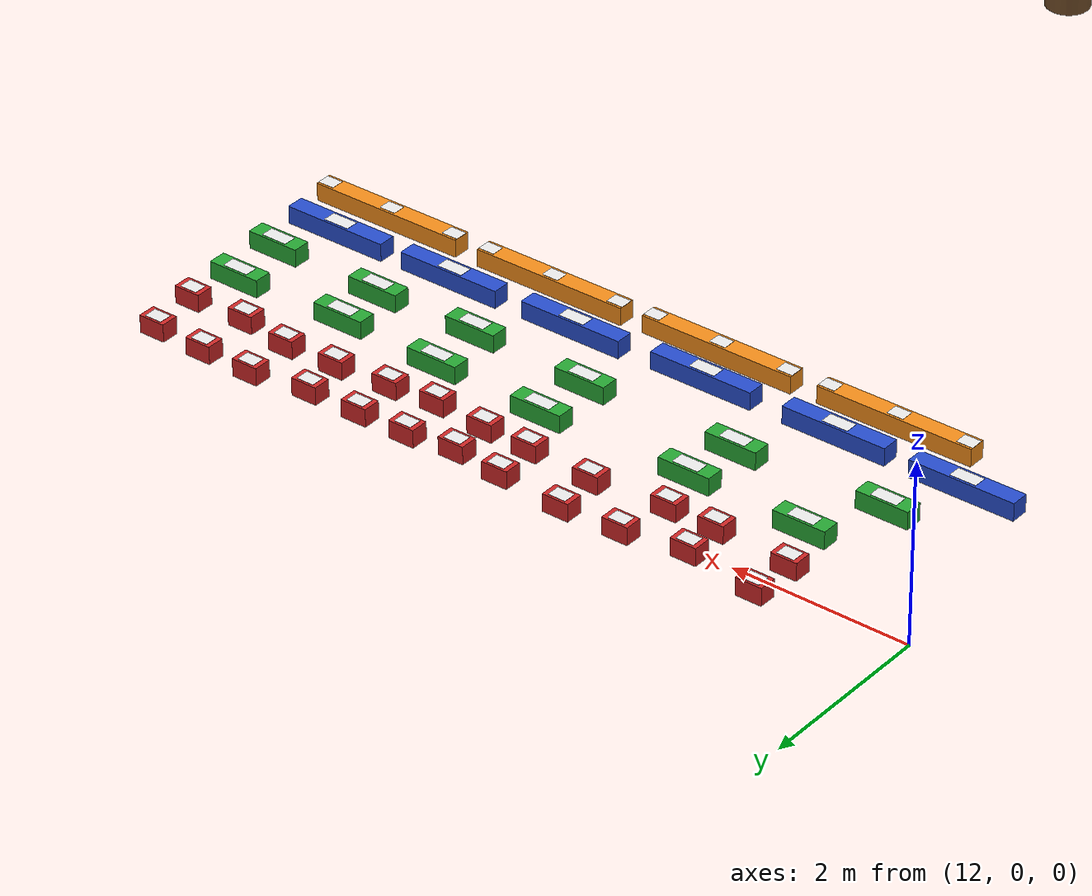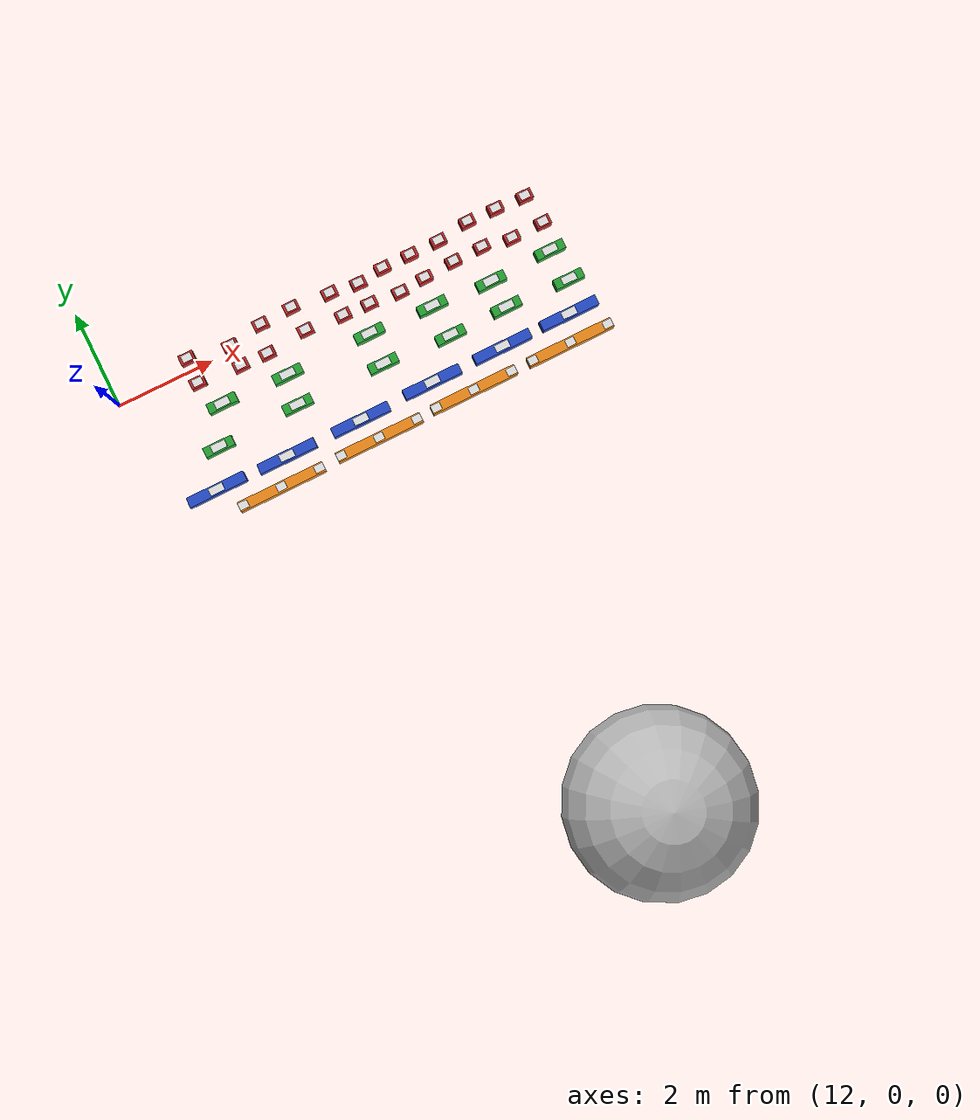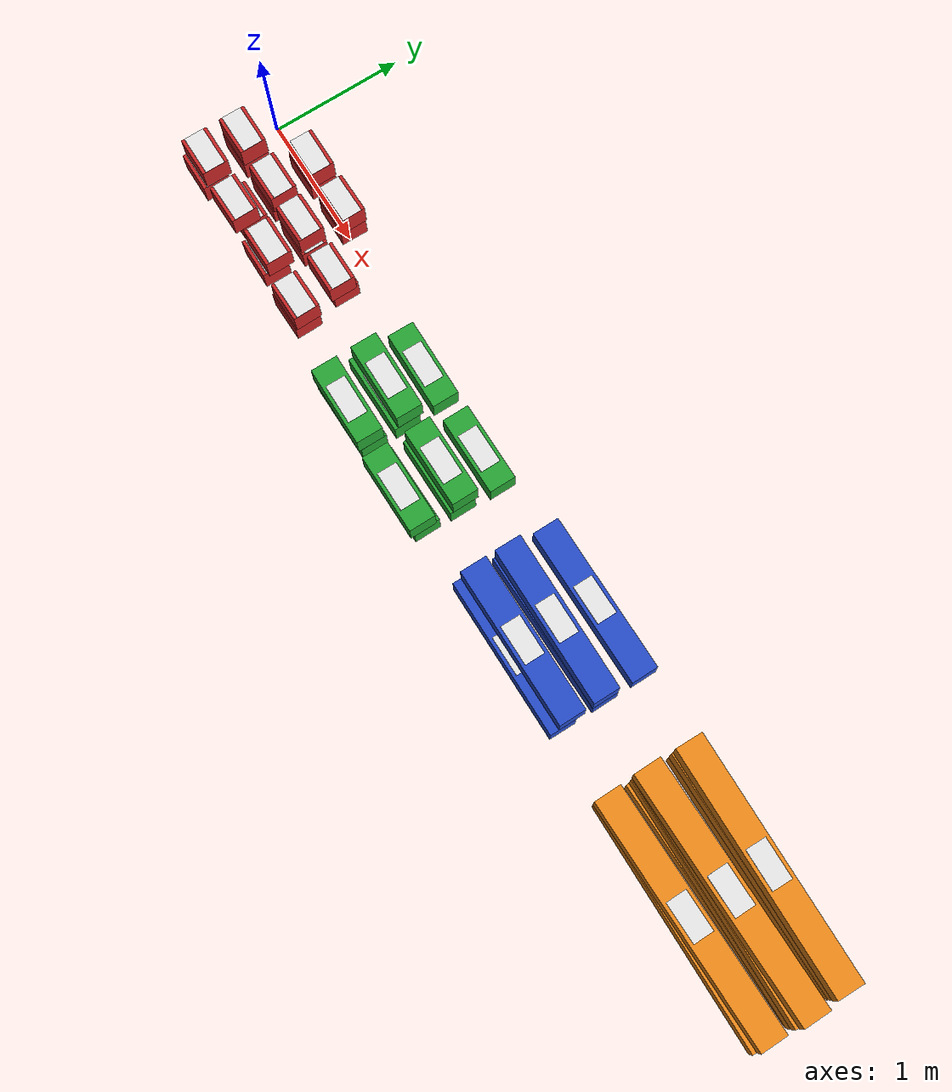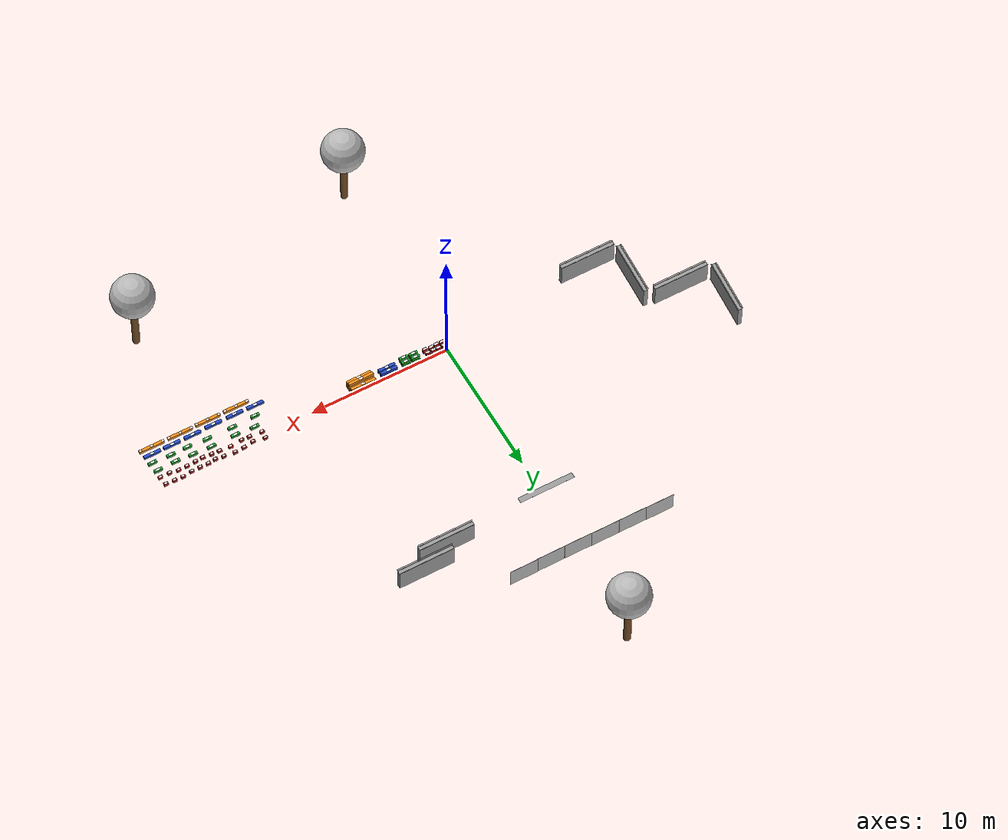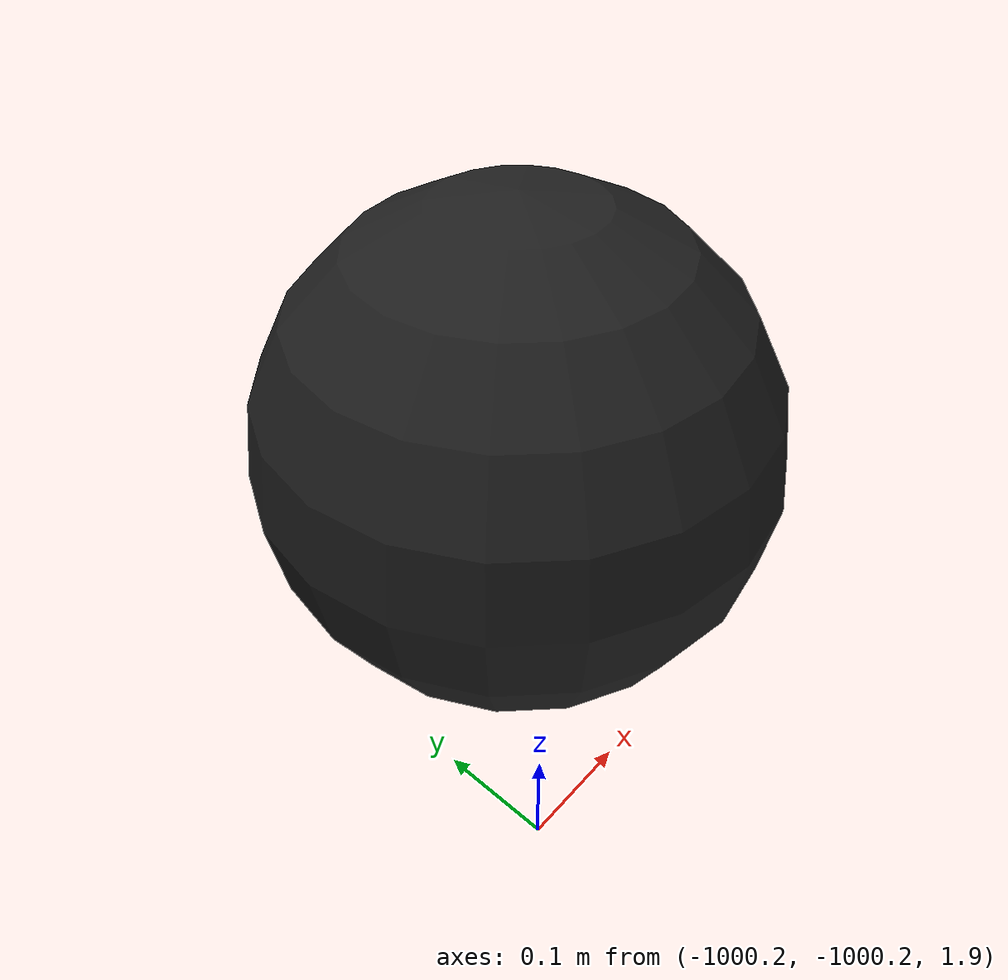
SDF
<sdf version="1.6">
 <world name="default">
  <plugin name="mrs_gazebo_static_transform_republisher_plugin" filename="libmrs_gazebo_static_transform_republisher.so"/>
  <spherical_coordinates>
   <surface_model>EARTH_WGS84</surface_model>
   <latitude_deg>37.4118</latitude_deg>
   <longitude_deg>-121.996</longitude_deg>
   <elevation>0</elevation>
   <heading_deg>0</heading_deg>
  </spherical_coordinates>
  <physics name="default_physics" default="0" type="ode">
   <ode>
    <solver>
     <type>quick</type>
     <iters>10</iters>
     <sor>1.3</sor>
     <use_dynamic_moi_rescaling>0</use_dynamic_moi_rescaling>
    </solver>
    <constraints>
     <cfm>0</cfm>
     <erp>0.2</erp>
     <contact_max_correcting_vel>1000</contact_max_correcting_vel>
     <contact_surface_layer>0.001</contact_surface_layer>
    </constraints>
   </ode>
   <max_step_size>0.004</max_step_size>
   <real_time_factor>1</real_time_factor>
   <real_time_update_rate>250</real_time_update_rate>
  </physics>
  <scene><shadows>0</shadows><ambient>0.4 0.4 0.4 1</ambient><background>0.7 0.7 0.7 1</background></scene>
  <light name="sun" type="directional">
   <pose>250 250 600 0 -0 0</pose>
   <diffuse>0.8 0.8 0.8 1</diffuse>
   <specular>0.2 0.2 0.2 1</specular>
   <attenuation>
    <range>1000</range>
    <constant>0.9</constant>
    <linear>0.01</linear>
    <quadratic>0.001</quadratic>
   </attenuation>
   <direction>0 0 -1</direction>
  </light>
  <model name="the_void">
   <static>1</static>
   <link name="link">
    <pose>0 0 0.1 0 -0 0</pose>
    <visual name="the_void">
     <pose>0 0 2 0 -0 0</pose>
     <geometry><sphere><radius>0.25</radius></sphere></geometry>
     <material>
      <script><uri>file://media/materials/scripts/Gazebo.material</uri><name>Gazebo/Black</name></script>
     </material>
    </visual>
   </link>
   <pose>-1000 -1000 0 0 -0 0</pose>
  </model>
  <plugin name="rviz_cam_synchronizer" filename="librviz_cam_synchronizer.so">
   <target_frame_id>gazebo_user_camera</target_frame_id>
   <world_origin_frame_id>uav1/gps_origin</world_origin_frame_id>
   <gazebo_camera_pose_topic>~/user_camera/pose</gazebo_camera_pose_topic>
   <target_frame_id>uav1::base_link</target_frame_id>
  </plugin>
  <gravity>0 0 -9.8066</gravity>
  <magnetic_field>6e-06 2.3e-05 -4.2e-05</magnetic_field>
  <atmosphere type="adiabatic"/>
  <audio><device>default</device></audio>
  <model name="brick_red_0">
   <static>1</static>
   <link name="link">
    <pose>0 0 0.1 0 -0 0</pose>
    <inertial>
     <mass>1</mass>
     <inertia>
      <ixx>0.00252984</ixx>
      <ixy>0</ixy>
      <ixz>0</ixz>
      <iyy>0.046802</iyy>
      <iyz>0</iyz>
      <izz>0.046802</izz>
     </inertia>
    </inertial>
    <visual name="main_box">
     <geometry><box><size>0.3 0.2 0.2</size></box></geometry>
     <material>
      <script><uri>file://media/materials/scripts/gazebo.material</uri><name>Gazebo/Red</name></script>
     </material>
    </visual>
    <visual name="white_plate">
     <pose>0 0 0.1 0 -0 0</pose>
     <geometry><box><size>0.3 0.15 0.006</size></box></geometry>
     <material>
      <script><uri>file://media/materials/scripts/gazebo.material</uri><name>Gazebo/White</name></script>
     </material>
    </visual>
    <collision name="collision"><geometry><box><size>0.3 0.2 0.2</size></box></geometry></collision>
   </link>
   <pose>0.059245 -0.274277 -0 0 -0 0.000913</pose>
  </model>
  <model name="brick_red_1">
   <static>1</static>
   <link name="link">
    <pose>0 0 0.1 0 -0 0</pose>
    <inertial>
     <mass>1</mass>
     <inertia>
      <ixx>0.00252984</ixx>
      <ixy>0</ixy>
      <ixz>0</ixz>
      <iyy>0.046802</iyy>
      <iyz>0</iyz>
      <izz>0.046802</izz>
     </inertia>
    </inertial>
    <visual name="main_box">
     <geometry><box><size>0.3 0.2 0.2</size></box></geometry>
     <material>
      <script><uri>file://media/materials/scripts/gazebo.material</uri><name>Gazebo/Red</name></script>
     </material>
    </visual>
    <visual name="white_plate">
     <pose>0 0 0.1 0 -0 0</pose>
     <geometry><box><size>0.3 0.15 0.006</size></box></geometry>
     <material>
      <script><uri>file://media/materials/scripts/gazebo.material</uri><name>Gazebo/White</name></script>
     </material>
    </visual>
    <collision name="collision"><geometry><box><size>0.3 0.2 0.2</size></box></geometry></collision>
   </link>
   <pose>0.059245 -0.270682 0.202 0 -0 0.00164</pose>
  </model>
  <model name="brick_red_2">
   <static>1</static>
   <link name="link">
    <pose>0 0 0.1 0 -0 0</pose>
    <inertial>
     <mass>1</mass>
     <inertia>
      <ixx>0.00252984</ixx>
      <ixy>0</ixy>
      <ixz>0</ixz>
      <iyy>0.046802</iyy>
      <iyz>0</iyz>
      <izz>0.046802</izz>
     </inertia>
    </inertial>
    <visual name="main_box">
     <geometry><box><size>0.3 0.2 0.2</size></box></geometry>
     <material>
      <script><uri>file://media/materials/scripts/gazebo.material</uri><name>Gazebo/Red</name></script>
     </material>
    </visual>
    <visual name="white_plate">
     <pose>0 0 0.1 0 -0 0</pose>
     <geometry><box><size>0.3 0.15 0.006</size></box></geometry>
     <material>
      <script><uri>file://media/materials/scripts/gazebo.material</uri><name>Gazebo/White</name></script>
     </material>
    </visual>
    <collision name="collision"><geometry><box><size>0.3 0.2 0.2</size></box></geometry></collision>
   </link>
   <pose>0.059245 -0.601932 -0 0 0 -0.005703</pose>
  </model>
  <model name="brick_red_3">
   <static>1</static>
   <link name="link">
    <pose>0 0 0.1 0 -0 0</pose>
    <inertial>
     <mass>1</mass>
     <inertia>
      <ixx>0.00252984</ixx>
      <ixy>0</ixy>
      <ixz>0</ixz>
      <iyy>0.046802</iyy>
      <iyz>0</iyz>
      <izz>0.046802</izz>
     </inertia>
    </inertial>
    <visual name="main_box">
     <geometry><box><size>0.3 0.2 0.2</size></box></geometry>
     <material>
      <script><uri>file://media/materials/scripts/gazebo.material</uri><name>Gazebo/Red</name></script>
     </material>
    </visual>
    <visual name="white_plate">
     <pose>0 0 0.1 0 -0 0</pose>
     <geometry><box><size>0.3 0.15 0.006</size></box></geometry>
     <material>
      <script><uri>file://media/materials/scripts/gazebo.material</uri><name>Gazebo/White</name></script>
     </material>
    </visual>
    <collision name="collision"><geometry><box><size>0.3 0.2 0.2</size></box></geometry></collision>
   </link>
   <pose>0.059245 -0.573208 0.202 0 0 -0.000976</pose>
  </model>
  <model name="brick_red_4">
   <static>1</static>
   <link name="link">
    <pose>0 0 0.1 0 -0 0</pose>
    <inertial>
     <mass>1</mass>
     <inertia>
      <ixx>0.00252984</ixx>
      <ixy>0</ixy>
      <ixz>0</ixz>
      <iyy>0.046802</iyy>
      <iyz>0</iyz>
      <izz>0.046802</izz>
     </inertia>
    </inertial>
    <visual name="main_box">
     <geometry><box><size>0.3 0.2 0.2</size></box></geometry>
     <material>
      <script><uri>file://media/materials/scripts/gazebo.material</uri><name>Gazebo/Red</name></script>
     </material>
    </visual>
    <visual name="white_plate">
     <pose>0 0 0.1 0 -0 0</pose>
     <geometry><box><size>0.3 0.15 0.006</size></box></geometry>
     <material>
      <script><uri>file://media/materials/scripts/gazebo.material</uri><name>Gazebo/White</name></script>
     </material>
    </visual>
    <collision name="collision"><geometry><box><size>0.3 0.2 0.2</size></box></geometry></collision>
   </link>
   <pose>0.455353 0.037849 0 0 0 -0.001435</pose>
  </model>
  <model name="brick_red_5">
   <static>1</static>
   <link name="link">
    <pose>0 0 0.1 0 -0 0</pose>
    <inertial>
     <mass>1</mass>
     <inertia>
      <ixx>0.00252984</ixx>
      <ixy>0</ixy>
      <ixz>0</ixz>
      <iyy>0.046802</iyy>
      <iyz>0</iyz>
      <izz>0.046802</izz>
     </inertia>
    </inertial>
    <visual name="main_box">
     <geometry><box><size>0.3 0.2 0.2</size></box></geometry>
     <material>
      <script><uri>file://media/materials/scripts/gazebo.material</uri><name>Gazebo/Red</name></script>
     </material>
    </visual>
    <visual name="white_plate">
     <pose>0 0 0.1 0 -0 0</pose>
     <geometry><box><size>0.3 0.15 0.006</size></box></geometry>
     <material>
      <script><uri>file://media/materials/scripts/gazebo.material</uri><name>Gazebo/White</name></script>
     </material>
    </visual>
    <collision name="collision"><geometry><box><size>0.3 0.2 0.2</size></box></geometry></collision>
   </link>
   <pose>0.469063 0.037849 0.202 0 0 -0.003653</pose>
  </model>
  <model name="brick_red_6">
   <static>1</static>
   <link name="link">
    <pose>0 0 0.1 0 -0 0</pose>
    <inertial>
     <mass>1</mass>
     <inertia>
      <ixx>0.00252984</ixx>
      <ixy>0</ixy>
      <ixz>0</ixz>
      <iyy>0.046802</iyy>
      <iyz>0</iyz>
      <izz>0.046802</izz>
     </inertia>
    </inertial>
    <visual name="main_box">
     <geometry><box><size>0.3 0.2 0.2</size></box></geometry>
     <material>
      <script><uri>file://media/materials/scripts/gazebo.material</uri><name>Gazebo/Red</name></script>
     </material>
    </visual>
    <visual name="white_plate">
     <pose>0 0 0.1 0 -0 0</pose>
     <geometry><box><size>0.3 0.15 0.006</size></box></geometry>
     <material>
      <script><uri>file://media/materials/scripts/gazebo.material</uri><name>Gazebo/White</name></script>
     </material>
    </visual>
    <collision name="collision"><geometry><box><size>0.3 0.2 0.2</size></box></geometry></collision>
   </link>
   <pose>0.458665 -0.278626 0 0 0 -0.000217</pose>
  </model>
  <model name="brick_red_7">
   <static>1</static>
   <link name="link">
    <pose>0 0 0.1 0 -0 0</pose>
    <inertial>
     <mass>1</mass>
     <inertia>
      <ixx>0.00252984</ixx>
      <ixy>0</ixy>
      <ixz>0</ixz>
      <iyy>0.046802</iyy>
      <iyz>0</iyz>
      <izz>0.046802</izz>
     </inertia>
    </inertial>
    <visual name="main_box">
     <geometry><box><size>0.3 0.2 0.2</size></box></geometry>
     <material>
      <script><uri>file://media/materials/scripts/gazebo.material</uri><name>Gazebo/Red</name></script>
     </material>
    </visual>
    <visual name="white_plate">
     <pose>0 0 0.1 0 -0 0</pose>
     <geometry><box><size>0.3 0.15 0.006</size></box></geometry>
     <material>
      <script><uri>file://media/materials/scripts/gazebo.material</uri><name>Gazebo/White</name></script>
     </material>
    </visual>
    <collision name="collision"><geometry><box><size>0.3 0.2 0.2</size></box></geometry></collision>
   </link>
   <pose>0.477688 -0.273226 0.202 0 -0 0.009959</pose>
  </model>
  <model name="brick_red_8">
   <static>1</static>
   <link name="link">
    <pose>0 0 0.1 0 -0 0</pose>
    <inertial>
     <mass>1</mass>
     <inertia>
      <ixx>0.00252984</ixx>
      <ixy>0</ixy>
      <ixz>0</ixz>
      <iyy>0.046802</iyy>
      <iyz>0</iyz>
      <izz>0.046802</izz>
     </inertia>
    </inertial>
    <visual name="main_box">
     <geometry><box><size>0.3 0.2 0.2</size></box></geometry>
     <material>
      <script><uri>file://media/materials/scripts/gazebo.material</uri><name>Gazebo/Red</name></script>
     </material>
    </visual>
    <visual name="white_plate">
     <pose>0 0 0.1 0 -0 0</pose>
     <geometry><box><size>0.3 0.15 0.006</size></box></geometry>
     <material>
      <script><uri>file://media/materials/scripts/gazebo.material</uri><name>Gazebo/White</name></script>
     </material>
    </visual>
    <collision name="collision"><geometry><box><size>0.3 0.2 0.2</size></box></geometry></collision>
   </link>
   <pose>0.460918 -0.526437 -0 0 -0 0.006094</pose>
  </model>
  <model name="brick_red_9">
   <static>1</static>
   <link name="link">
    <pose>0 0 0.1 0 -0 0</pose>
    <inertial>
     <mass>1</mass>
     <inertia>
      <ixx>0.00252984</ixx>
      <ixy>0</ixy>
      <ixz>0</ixz>
      <iyy>0.046802</iyy>
      <iyz>0</iyz>
      <izz>0.046802</izz>
     </inertia>
    </inertial>
    <visual name="main_box">
     <geometry><box><size>0.3 0.2 0.2</size></box></geometry>
     <material>
      <script><uri>file://media/materials/scripts/gazebo.material</uri><name>Gazebo/Red</name></script>
     </material>
    </visual>
    <visual name="white_plate">
     <pose>0 0 0.1 0 -0 0</pose>
     <geometry><box><size>0.3 0.15 0.006</size></box></geometry>
     <material>
      <script><uri>file://media/materials/scripts/gazebo.material</uri><name>Gazebo/White</name></script>
     </material>
    </visual>
    <collision name="collision"><geometry><box><size>0.3 0.2 0.2</size></box></geometry></collision>
   </link>
   <pose>0.473201 -0.583135 0.202 0 -0 0.014849</pose>
  </model>
  <model name="brick_red_10">
   <static>1</static>
   <link name="link">
    <pose>0 0 0.1 0 -0 0</pose>
    <inertial>
     <mass>1</mass>
     <inertia>
      <ixx>0.00252984</ixx>
      <ixy>0</ixy>
      <ixz>0</ixz>
      <iyy>0.046802</iyy>
      <iyz>0</iyz>
      <izz>0.046802</izz>
     </inertia>
    </inertial>
    <visual name="main_box">
     <geometry><box><size>0.3 0.2 0.2</size></box></geometry>
     <material>
      <script><uri>file://media/materials/scripts/gazebo.material</uri><name>Gazebo/Red</name></script>
     </material>
    </visual>
    <visual name="white_plate">
     <pose>0 0 0.1 0 -0 0</pose>
     <geometry><box><size>0.3 0.15 0.006</size></box></geometry>
     <material>
      <script><uri>file://media/materials/scripts/gazebo.material</uri><name>Gazebo/White</name></script>
     </material>
    </visual>
    <collision name="collision"><geometry><box><size>0.3 0.2 0.2</size></box></geometry></collision>
   </link>
   <pose>0.868164 0.037849 -0 0 0 -0.012876</pose>
  </model>
  <model name="brick_red_11">
   <static>1</static>
   <link name="link">
    <pose>0 0 0.1 0 -0 0</pose>
    <inertial>
     <mass>1</mass>
     <inertia>
      <ixx>0.00252984</ixx>
      <ixy>0</ixy>
      <ixz>0</ixz>
      <iyy>0.046802</iyy>
      <iyz>0</iyz>
      <izz>0.046802</izz>
     </inertia>
    </inertial>
    <visual name="main_box">
     <geometry><box><size>0.3 0.2 0.2</size></box></geometry>
     <material>
      <script><uri>file://media/materials/scripts/gazebo.material</uri><name>Gazebo/Red</name></script>
     </material>
    </visual>
    <visual name="white_plate">
     <pose>0 0 0.1 0 -0 0</pose>
     <geometry><box><size>0.3 0.15 0.006</size></box></geometry>
     <material>
      <script><uri>file://media/materials/scripts/gazebo.material</uri><name>Gazebo/White</name></script>
     </material>
    </visual>
    <collision name="collision"><geometry><box><size>0.3 0.2 0.2</size></box></geometry></collision>
   </link>
   <pose>0.879277 0.037849 0.202 0 -0 0.014297</pose>
  </model>
  <model name="brick_red_12">
   <static>1</static>
   <link name="link">
    <pose>0 0 0.1 0 -0 0</pose>
    <inertial>
     <mass>1</mass>
     <inertia>
      <ixx>0.00252984</ixx>
      <ixy>0</ixy>
      <ixz>0</ixz>
      <iyy>0.046802</iyy>
      <iyz>0</iyz>
      <izz>0.046802</izz>
     </inertia>
    </inertial>
    <visual name="main_box">
     <geometry><box><size>0.3 0.2 0.2</size></box></geometry>
     <material>
      <script><uri>file://media/materials/scripts/gazebo.material</uri><name>Gazebo/Red</name></script>
     </material>
    </visual>
    <visual name="white_plate">
     <pose>0 0 0.1 0 -0 0</pose>
     <geometry><box><size>0.3 0.15 0.006</size></box></geometry>
     <material>
      <script><uri>file://media/materials/scripts/gazebo.material</uri><name>Gazebo/White</name></script>
     </material>
    </visual>
    <collision name="collision"><geometry><box><size>0.3 0.2 0.2</size></box></geometry></collision>
   </link>
   <pose>0.863916 -0.277629 -0 0 -0 0.005086</pose>
  </model>
  <model name="brick_red_13">
   <static>1</static>
   <link name="link">
    <pose>0 0 0.1 0 -0 0</pose>
    <inertial>
     <mass>1</mass>
     <inertia>
      <ixx>0.00252984</ixx>
      <ixy>0</ixy>
      <ixz>0</ixz>
      <iyy>0.046802</iyy>
      <iyz>0</iyz>
      <izz>0.046802</izz>
     </inertia>
    </inertial>
    <visual name="main_box">
     <geometry><box><size>0.3 0.2 0.2</size></box></geometry>
     <material>
      <script><uri>file://media/materials/scripts/gazebo.material</uri><name>Gazebo/Red</name></script>
     </material>
    </visual>
    <visual name="white_plate">
     <pose>0 0 0.1 0 -0 0</pose>
     <geometry><box><size>0.3 0.15 0.006</size></box></geometry>
     <material>
      <script><uri>file://media/materials/scripts/gazebo.material</uri><name>Gazebo/White</name></script>
     </material>
    </visual>
    <collision name="collision"><geometry><box><size>0.3 0.2 0.2</size></box></geometry></collision>
   </link>
   <pose>0.845682 -0.273405 0.202 0 -0 0.013202</pose>
  </model>
  <model name="brick_red_14">
   <static>1</static>
   <link name="link">
    <pose>0 0 0.1 0 -0 0</pose>
    <inertial>
     <mass>1</mass>
     <inertia>
      <ixx>0.00252984</ixx>
      <ixy>0</ixy>
      <ixz>0</ixz>
      <iyy>0.046802</iyy>
      <iyz>0</iyz>
      <izz>0.046802</izz>
     </inertia>
    </inertial>
    <visual name="main_box">
     <geometry><box><size>0.3 0.2 0.2</size></box></geometry>
     <material>
      <script><uri>file://media/materials/scripts/gazebo.material</uri><name>Gazebo/Red</name></script>
     </material>
    </visual>
    <visual name="white_plate">
     <pose>0 0 0.1 0 -0 0</pose>
     <geometry><box><size>0.3 0.15 0.006</size></box></geometry>
     <material>
      <script><uri>file://media/materials/scripts/gazebo.material</uri><name>Gazebo/White</name></script>
     </material>
    </visual>
    <collision name="collision"><geometry><box><size>0.3 0.2 0.2</size></box></geometry></collision>
   </link>
   <pose>0.849971 -0.581345 -0 0 0 -0.010727</pose>
  </model>
  <model name="brick_red_15">
   <static>1</static>
   <link name="link">
    <pose>0 0 0.1 0 -0 0</pose>
    <inertial>
     <mass>1</mass>
     <inertia>
      <ixx>0.00252984</ixx>
      <ixy>0</ixy>
      <ixz>0</ixz>
      <iyy>0.046802</iyy>
      <iyz>0</iyz>
      <izz>0.046802</izz>
     </inertia>
    </inertial>
    <visual name="main_box">
     <geometry><box><size>0.3 0.2 0.2</size></box></geometry>
     <material>
      <script><uri>file://media/materials/scripts/gazebo.material</uri><name>Gazebo/Red</name></script>
     </material>
    </visual>
    <visual name="white_plate">
     <pose>0 0 0.1 0 -0 0</pose>
     <geometry><box><size>0.3 0.15 0.006</size></box></geometry>
     <material>
      <script><uri>file://media/materials/scripts/gazebo.material</uri><name>Gazebo/White</name></script>
     </material>
    </visual>
    <collision name="collision"><geometry><box><size>0.3 0.2 0.2</size></box></geometry></collision>
   </link>
   <pose>0.875162 -0.547991 0.202 0 -0 0.003486</pose>
  </model>
  <model name="brick_red_16">
   <static>1</static>
   <link name="link">
    <pose>0 0 0.1 0 -0 0</pose>
    <inertial>
     <mass>1</mass>
     <inertia>
      <ixx>0.00252984</ixx>
      <ixy>0</ixy>
      <ixz>0</ixz>
      <iyy>0.046802</iyy>
      <iyz>0</iyz>
      <izz>0.046802</izz>
     </inertia>
    </inertial>
    <visual name="main_box">
     <geometry><box><size>0.3 0.2 0.2</size></box></geometry>
     <material>
      <script><uri>file://media/materials/scripts/gazebo.material</uri><name>Gazebo/Red</name></script>
     </material>
    </visual>
    <visual name="white_plate">
     <pose>0 0 0.1 0 -0 0</pose>
     <geometry><box><size>0.3 0.15 0.006</size></box></geometry>
     <material>
      <script><uri>file://media/materials/scripts/gazebo.material</uri><name>Gazebo/White</name></script>
     </material>
    </visual>
    <collision name="collision"><geometry><box><size>0.3 0.2 0.2</size></box></geometry></collision>
   </link>
   <pose>1.24497 -0.253858 0 0 -0 0.000118</pose>
  </model>
  <model name="brick_red_17">
   <static>1</static>
   <link name="link">
    <pose>0 0 0.1 0 -0 0</pose>
    <inertial>
     <mass>1</mass>
     <inertia>
      <ixx>0.00252984</ixx>
      <ixy>0</ixy>
      <ixz>0</ixz>
      <iyy>0.046802</iyy>
      <iyz>0</iyz>
      <izz>0.046802</izz>
     </inertia>
    </inertial>
    <visual name="main_box">
     <geometry><box><size>0.3 0.2 0.2</size></box></geometry>
     <material>
      <script><uri>file://media/materials/scripts/gazebo.material</uri><name>Gazebo/Red</name></script>
     </material>
    </visual>
    <visual name="white_plate">
     <pose>0 0 0.1 0 -0 0</pose>
     <geometry><box><size>0.3 0.15 0.006</size></box></geometry>
     <material>
      <script><uri>file://media/materials/scripts/gazebo.material</uri><name>Gazebo/White</name></script>
     </material>
    </visual>
    <collision name="collision"><geometry><box><size>0.3 0.2 0.2</size></box></geometry></collision>
   </link>
   <pose>1.2709 -0.281558 0.202 0 0 -0.001797</pose>
  </model>
  <model name="brick_red_18">
   <static>1</static>
   <link name="link">
    <pose>0 0 0.1 0 -0 0</pose>
    <inertial>
     <mass>1</mass>
     <inertia>
      <ixx>0.00252984</ixx>
      <ixy>0</ixy>
      <ixz>0</ixz>
      <iyy>0.046802</iyy>
      <iyz>0</iyz>
      <izz>0.046802</izz>
     </inertia>
    </inertial>
    <visual name="main_box">
     <geometry><box><size>0.3 0.2 0.2</size></box></geometry>
     <material>
      <script><uri>file://media/materials/scripts/gazebo.material</uri><name>Gazebo/Red</name></script>
     </material>
    </visual>
    <visual name="white_plate">
     <pose>0 0 0.1 0 -0 0</pose>
     <geometry><box><size>0.3 0.15 0.006</size></box></geometry>
     <material>
      <script><uri>file://media/materials/scripts/gazebo.material</uri><name>Gazebo/White</name></script>
     </material>
    </visual>
    <collision name="collision"><geometry><box><size>0.3 0.2 0.2</size></box></geometry></collision>
   </link>
   <pose>1.30078 -0.598432 0 0 -0 0.01377</pose>
  </model>
  <model name="brick_red_19">
   <static>1</static>
   <link name="link">
    <pose>0 0 0.1 0 -0 0</pose>
    <inertial>
     <mass>1</mass>
     <inertia>
      <ixx>0.00252984</ixx>
      <ixy>0</ixy>
      <ixz>0</ixz>
      <iyy>0.046802</iyy>
      <iyz>0</iyz>
      <izz>0.046802</izz>
     </inertia>
    </inertial>
    <visual name="main_box">
     <geometry><box><size>0.3 0.2 0.2</size></box></geometry>
     <material>
      <script><uri>file://media/materials/scripts/gazebo.material</uri><name>Gazebo/Red</name></script>
     </material>
    </visual>
    <visual name="white_plate">
     <pose>0 0 0.1 0 -0 0</pose>
     <geometry><box><size>0.3 0.15 0.006</size></box></geometry>
     <material>
      <script><uri>file://media/materials/scripts/gazebo.material</uri><name>Gazebo/White</name></script>
     </material>
    </visual>
    <collision name="collision"><geometry><box><size>0.3 0.2 0.2</size></box></geometry></collision>
   </link>
   <pose>1.31711 -0.592665 0.202 0 -0 0.012895</pose>
  </model>
  <model name="brick_green_20">
   <static>1</static>
   <link name="link">
    <pose>0 0 0.1 0 -0 0</pose>
    <inertial>
     <mass>1</mass>
     <inertia>
      <ixx>0.00252984</ixx>
      <ixy>0</ixy>
      <ixz>0</ixz>
      <iyy>0.046802</iyy>
      <iyz>0</iyz>
      <izz>0.046802</izz>
     </inertia>
    </inertial>
    <visual name="main_box">
     <geometry><box><size>0.6 0.2 0.2</size></box></geometry>
     <material>
      <script><uri>file://media/materials/scripts/gazebo.material</uri><name>Gazebo/Green</name></script>
     </material>
    </visual>
    <visual name="white_plate">
     <pose>0 0 0.1 0 -0 0</pose>
     <geometry><box><size>0.3 0.15 0.006</size></box></geometry>
     <material>
      <script><uri>file://media/materials/scripts/gazebo.material</uri><name>Gazebo/White</name></script>
     </material>
    </visual>
    <collision name="collision"><geometry><box><size>0.6 0.2 0.2</size></box></geometry></collision>
   </link>
   <pose>2.14444 -0.090797 -0 0 0 -0.011736</pose>
  </model>
  <model name="brick_green_21">
   <static>1</static>
   <link name="link">
    <pose>0 0 0.1 0 -0 0</pose>
    <inertial>
     <mass>1</mass>
     <inertia>
      <ixx>0.00252984</ixx>
      <ixy>0</ixy>
      <ixz>0</ixz>
      <iyy>0.046802</iyy>
      <iyz>0</iyz>
      <izz>0.046802</izz>
     </inertia>
    </inertial>
    <visual name="main_box">
     <geometry><box><size>0.6 0.2 0.2</size></box></geometry>
     <material>
      <script><uri>file://media/materials/scripts/gazebo.material</uri><name>Gazebo/Green</name></script>
     </material>
    </visual>
    <visual name="white_plate">
     <pose>0 0 0.1 0 -0 0</pose>
     <geometry><box><size>0.3 0.15 0.006</size></box></geometry>
     <material>
      <script><uri>file://media/materials/scripts/gazebo.material</uri><name>Gazebo/White</name></script>
     </material>
    </visual>
    <collision name="collision"><geometry><box><size>0.6 0.2 0.2</size></box></geometry></collision>
   </link>
   <pose>2.14444 -0.403337 0 0 -0 0.004379</pose>
  </model>
  <model name="brick_green_22">
   <static>1</static>
   <link name="link">
    <pose>0 0 0.1 0 -0 0</pose>
    <inertial>
     <mass>1</mass>
     <inertia>
      <ixx>0.00252984</ixx>
      <ixy>0</ixy>
      <ixz>0</ixz>
      <iyy>0.046802</iyy>
      <iyz>0</iyz>
      <izz>0.046802</izz>
     </inertia>
    </inertial>
    <visual name="main_box">
     <geometry><box><size>0.6 0.2 0.2</size></box></geometry>
     <material>
      <script><uri>file://media/materials/scripts/gazebo.material</uri><name>Gazebo/Green</name></script>
     </material>
    </visual>
    <visual name="white_plate">
     <pose>0 0 0.1 0 -0 0</pose>
     <geometry><box><size>0.3 0.15 0.006</size></box></geometry>
     <material>
      <script><uri>file://media/materials/scripts/gazebo.material</uri><name>Gazebo/White</name></script>
     </material>
    </visual>
    <collision name="collision"><geometry><box><size>0.6 0.2 0.2</size></box></geometry></collision>
   </link>
   <pose>2.14444 -0.372656 0.202 0 0 -0.007074</pose>
  </model>
  <model name="brick_green_23">
   <static>1</static>
   <link name="link">
    <pose>0 0 0.1 0 -0 0</pose>
    <inertial>
     <mass>1</mass>
     <inertia>
      <ixx>0.00252984</ixx>
      <ixy>0</ixy>
      <ixz>0</ixz>
      <iyy>0.046802</iyy>
      <iyz>0</iyz>
      <izz>0.046802</izz>
     </inertia>
    </inertial>
    <visual name="main_box">
     <geometry><box><size>0.6 0.2 0.2</size></box></geometry>
     <material>
      <script><uri>file://media/materials/scripts/gazebo.material</uri><name>Gazebo/Green</name></script>
     </material>
    </visual>
    <visual name="white_plate">
     <pose>0 0 0.1 0 -0 0</pose>
     <geometry><box><size>0.3 0.15 0.006</size></box></geometry>
     <material>
      <script><uri>file://media/materials/scripts/gazebo.material</uri><name>Gazebo/White</name></script>
     </material>
    </visual>
    <collision name="collision"><geometry><box><size>0.6 0.2 0.2</size></box></geometry></collision>
   </link>
   <pose>2.14444 -0.669911 -0 0 -0 0.002734</pose>
  </model>
  <model name="brick_green_24">
   <static>1</static>
   <link name="link">
    <pose>0 0 0.1 0 -0 0</pose>
    <inertial>
     <mass>1</mass>
     <inertia>
      <ixx>0.00252984</ixx>
      <ixy>0</ixy>
      <ixz>0</ixz>
      <iyy>0.046802</iyy>
      <iyz>0</iyz>
      <izz>0.046802</izz>
     </inertia>
    </inertial>
    <visual name="main_box">
     <geometry><box><size>0.6 0.2 0.2</size></box></geometry>
     <material>
      <script><uri>file://media/materials/scripts/gazebo.material</uri><name>Gazebo/Green</name></script>
     </material>
    </visual>
    <visual name="white_plate">
     <pose>0 0 0.1 0 -0 0</pose>
     <geometry><box><size>0.3 0.15 0.006</size></box></geometry>
     <material>
      <script><uri>file://media/materials/scripts/gazebo.material</uri><name>Gazebo/White</name></script>
     </material>
    </visual>
    <collision name="collision"><geometry><box><size>0.6 0.2 0.2</size></box></geometry></collision>
   </link>
   <pose>2.14444 -0.684596 0.202 0 0 -0.008299</pose>
  </model>
  <model name="brick_green_25">
   <static>1</static>
   <link name="link">
    <pose>0 0 0.1 0 -0 0</pose>
    <inertial>
     <mass>1</mass>
     <inertia>
      <ixx>0.00252984</ixx>
      <ixy>0</ixy>
      <ixz>0</ixz>
      <iyy>0.046802</iyy>
      <iyz>0</iyz>
      <izz>0.046802</izz>
     </inertia>
    </inertial>
    <visual name="main_box">
     <geometry><box><size>0.6 0.2 0.2</size></box></geometry>
     <material>
      <script><uri>file://media/materials/scripts/gazebo.material</uri><name>Gazebo/Green</name></script>
     </material>
    </visual>
    <visual name="white_plate">
     <pose>0 0 0.1 0 -0 0</pose>
     <geometry><box><size>0.3 0.15 0.006</size></box></geometry>
     <material>
      <script><uri>file://media/materials/scripts/gazebo.material</uri><name>Gazebo/White</name></script>
     </material>
    </visual>
    <collision name="collision"><geometry><box><size>0.6 0.2 0.2</size></box></geometry></collision>
   </link>
   <pose>2.86276 -0.090797 0 0 -0 0.001473</pose>
  </model>
  <model name="brick_green_26">
   <static>1</static>
   <link name="link">
    <pose>0 0 0.1 0 -0 0</pose>
    <inertial>
     <mass>1</mass>
     <inertia>
      <ixx>0.00252984</ixx>
      <ixy>0</ixy>
      <ixz>0</ixz>
      <iyy>0.046802</iyy>
      <iyz>0</iyz>
      <izz>0.046802</izz>
     </inertia>
    </inertial>
    <visual name="main_box">
     <geometry><box><size>0.6 0.2 0.2</size></box></geometry>
     <material>
      <script><uri>file://media/materials/scripts/gazebo.material</uri><name>Gazebo/Green</name></script>
     </material>
    </visual>
    <visual name="white_plate">
     <pose>0 0 0.1 0 -0 0</pose>
     <geometry><box><size>0.3 0.15 0.006</size></box></geometry>
     <material>
      <script><uri>file://media/materials/scripts/gazebo.material</uri><name>Gazebo/White</name></script>
     </material>
    </visual>
    <collision name="collision"><geometry><box><size>0.6 0.2 0.2</size></box></geometry></collision>
   </link>
   <pose>2.8464 -0.398579 0 0 -0 0.005057</pose>
  </model>
  <model name="brick_green_27">
   <static>1</static>
   <link name="link">
    <pose>0 0 0.1 0 -0 0</pose>
    <inertial>
     <mass>1</mass>
     <inertia>
      <ixx>0.00252984</ixx>
      <ixy>0</ixy>
      <ixz>0</ixz>
      <iyy>0.046802</iyy>
      <iyz>0</iyz>
      <izz>0.046802</izz>
     </inertia>
    </inertial>
    <visual name="main_box">
     <geometry><box><size>0.6 0.2 0.2</size></box></geometry>
     <material>
      <script><uri>file://media/materials/scripts/gazebo.material</uri><name>Gazebo/Green</name></script>
     </material>
    </visual>
    <visual name="white_plate">
     <pose>0 0 0.1 0 -0 0</pose>
     <geometry><box><size>0.3 0.15 0.006</size></box></geometry>
     <material>
      <script><uri>file://media/materials/scripts/gazebo.material</uri><name>Gazebo/White</name></script>
     </material>
    </visual>
    <collision name="collision"><geometry><box><size>0.6 0.2 0.2</size></box></geometry></collision>
   </link>
   <pose>2.84819 -0.377098 0.202 0 -0 0.004954</pose>
  </model>
  <model name="brick_green_28">
   <static>1</static>
   <link name="link">
    <pose>0 0 0.1 0 -0 0</pose>
    <inertial>
     <mass>1</mass>
     <inertia>
      <ixx>0.00252984</ixx>
      <ixy>0</ixy>
      <ixz>0</ixz>
      <iyy>0.046802</iyy>
      <iyz>0</iyz>
      <izz>0.046802</izz>
     </inertia>
    </inertial>
    <visual name="main_box">
     <geometry><box><size>0.6 0.2 0.2</size></box></geometry>
     <material>
      <script><uri>file://media/materials/scripts/gazebo.material</uri><name>Gazebo/Green</name></script>
     </material>
    </visual>
    <visual name="white_plate">
     <pose>0 0 0.1 0 -0 0</pose>
     <geometry><box><size>0.3 0.15 0.006</size></box></geometry>
     <material>
      <script><uri>file://media/materials/scripts/gazebo.material</uri><name>Gazebo/White</name></script>
     </material>
    </visual>
    <collision name="collision"><geometry><box><size>0.6 0.2 0.2</size></box></geometry></collision>
   </link>
   <pose>2.8394 -0.68106 0 0 -0 0.011618</pose>
  </model>
  <model name="brick_green_29">
   <static>1</static>
   <link name="link">
    <pose>0 0 0.1 0 -0 0</pose>
    <inertial>
     <mass>1</mass>
     <inertia>
      <ixx>0.00252984</ixx>
      <ixy>0</ixy>
      <ixz>0</ixz>
      <iyy>0.046802</iyy>
      <iyz>0</iyz>
      <izz>0.046802</izz>
     </inertia>
    </inertial>
    <visual name="main_box">
     <geometry><box><size>0.6 0.2 0.2</size></box></geometry>
     <material>
      <script><uri>file://media/materials/scripts/gazebo.material</uri><name>Gazebo/Green</name></script>
     </material>
    </visual>
    <visual name="white_plate">
     <pose>0 0 0.1 0 -0 0</pose>
     <geometry><box><size>0.3 0.15 0.006</size></box></geometry>
     <material>
      <script><uri>file://media/materials/scripts/gazebo.material</uri><name>Gazebo/White</name></script>
     </material>
    </visual>
    <collision name="collision"><geometry><box><size>0.6 0.2 0.2</size></box></geometry></collision>
   </link>
   <pose>2.84868 -0.710199 0.202 0 -0 0.001337</pose>
  </model>
  <model name="brick_blue_30">
   <static>1</static>
   <link name="link">
    <pose>0 0 0.1 0 -0 0</pose>
    <inertial>
     <mass>1.5</mass>
     <inertia>
      <ixx>0.00252984</ixx>
      <ixy>0</ixy>
      <ixz>0</ixz>
      <iyy>0.046802</iyy>
      <iyz>0</iyz>
      <izz>0.046802</izz>
     </inertia>
    </inertial>
    <visual name="main_box">
     <geometry><box><size>1.2 0.2 0.2</size></box></geometry>
     <material>
      <script><uri>file://media/materials/scripts/gazebo.material</uri><name>Gazebo/Blue</name></script>
     </material>
    </visual>
    <visual name="white_plate">
     <pose>0 0 0.1 0 -0 0</pose>
     <geometry><box><size>0.3 0.15 0.006</size></box></geometry>
     <material>
      <script><uri>file://media/materials/scripts/gazebo.material</uri><name>Gazebo/White</name></script>
     </material>
    </visual>
    <collision name="collision"><geometry><box><size>1.2 0.2 0.2</size></box></geometry></collision>
   </link>
   <pose>4.15925 -0.002355 0 0 -0 0.003169</pose>
  </model>
  <model name="brick_blue_31">
   <static>1</static>
   <link name="link">
    <pose>0 0 0.1 0 -0 0</pose>
    <inertial>
     <mass>1.5</mass>
     <inertia>
      <ixx>0.00252984</ixx>
      <ixy>0</ixy>
      <ixz>0</ixz>
      <iyy>0.046802</iyy>
      <iyz>0</iyz>
      <izz>0.046802</izz>
     </inertia>
    </inertial>
    <visual name="main_box">
     <geometry><box><size>1.2 0.2 0.2</size></box></geometry>
     <material>
      <script><uri>file://media/materials/scripts/gazebo.material</uri><name>Gazebo/Blue</name></script>
     </material>
    </visual>
    <visual name="white_plate">
     <pose>0 0 0.1 0 -0 0</pose>
     <geometry><box><size>0.3 0.15 0.006</size></box></geometry>
     <material>
      <script><uri>file://media/materials/scripts/gazebo.material</uri><name>Gazebo/White</name></script>
     </material>
    </visual>
    <collision name="collision"><geometry><box><size>1.2 0.2 0.2</size></box></geometry></collision>
   </link>
   <pose>4.15925 -0.317438 0 0 -0 0.012274</pose>
  </model>
  <model name="brick_blue_32">
   <static>1</static>
   <link name="link">
    <pose>0 0 0.1 0 -0 0</pose>
    <inertial>
     <mass>1.5</mass>
     <inertia>
      <ixx>0.00252984</ixx>
      <ixy>0</ixy>
      <ixz>0</ixz>
      <iyy>0.046802</iyy>
      <iyz>0</iyz>
      <izz>0.046802</izz>
     </inertia>
    </inertial>
    <visual name="main_box">
     <geometry><box><size>1.2 0.2 0.2</size></box></geometry>
     <material>
      <script><uri>file://media/materials/scripts/gazebo.material</uri><name>Gazebo/Blue</name></script>
     </material>
    </visual>
    <visual name="white_plate">
     <pose>0 0 0.1 0 -0 0</pose>
     <geometry><box><size>0.3 0.15 0.006</size></box></geometry>
     <material>
      <script><uri>file://media/materials/scripts/gazebo.material</uri><name>Gazebo/White</name></script>
     </material>
    </visual>
    <collision name="collision"><geometry><box><size>1.2 0.2 0.2</size></box></geometry></collision>
   </link>
   <pose>4.15925 -0.310888 0.202 0 0 -0.005419</pose>
  </model>
  <model name="brick_blue_33">
   <static>1</static>
   <link name="link">
    <pose>0 0 0.1 0 -0 0</pose>
    <inertial>
     <mass>1.5</mass>
     <inertia>
      <ixx>0.00252984</ixx>
      <ixy>0</ixy>
      <ixz>0</ixz>
      <iyy>0.046802</iyy>
      <iyz>0</iyz>
      <izz>0.046802</izz>
     </inertia>
    </inertial>
    <visual name="main_box">
     <geometry><box><size>1.2 0.2 0.2</size></box></geometry>
     <material>
      <script><uri>file://media/materials/scripts/gazebo.material</uri><name>Gazebo/Blue</name></script>
     </material>
    </visual>
    <visual name="white_plate">
     <pose>0 0 0.1 0 -0 0</pose>
     <geometry><box><size>0.3 0.15 0.006</size></box></geometry>
     <material>
      <script><uri>file://media/materials/scripts/gazebo.material</uri><name>Gazebo/White</name></script>
     </material>
    </visual>
    <collision name="collision"><geometry><box><size>1.2 0.2 0.2</size></box></geometry></collision>
   </link>
   <pose>4.15925 -0.640042 0 0 0 -0.002377</pose>
  </model>
  <model name="brick_blue_34">
   <static>1</static>
   <link name="link">
    <pose>0 0 0.1 0 -0 0</pose>
    <inertial>
     <mass>1.5</mass>
     <inertia>
      <ixx>0.00252984</ixx>
      <ixy>0</ixy>
      <ixz>0</ixz>
      <iyy>0.046802</iyy>
      <iyz>0</iyz>
      <izz>0.046802</izz>
     </inertia>
    </inertial>
    <visual name="main_box">
     <geometry><box><size>1.2 0.2 0.2</size></box></geometry>
     <material>
      <script><uri>file://media/materials/scripts/gazebo.material</uri><name>Gazebo/Blue</name></script>
     </material>
    </visual>
    <visual name="white_plate">
     <pose>0 0 0.1 0 -0 0</pose>
     <geometry><box><size>0.3 0.15 0.006</size></box></geometry>
     <material>
      <script><uri>file://media/materials/scripts/gazebo.material</uri><name>Gazebo/White</name></script>
     </material>
    </visual>
    <collision name="collision"><geometry><box><size>1.2 0.2 0.2</size></box></geometry></collision>
   </link>
   <pose>4.15925 -0.575449 0.202 0 0 -0.001274</pose>
  </model>
  <model name="brick_orange_35">
   <static>1</static>
   <link name="link">
    <pose>0 0 0.1 0 -0 0</pose>
    <inertial>
     <mass>2</mass>
     <inertia>
      <ixx>0.00252984</ixx>
      <ixy>0</ixy>
      <ixz>0</ixz>
      <iyy>0.046802</iyy>
      <iyz>0</iyz>
      <izz>0.046802</izz>
     </inertia>
    </inertial>
    <visual name="main_box">
     <geometry><box><size>1.8 0.2 0.2</size></box></geometry>
     <material>
      <script><uri>file://media/materials/scripts/gazebo.material</uri><name>Gazebo/Orange</name></script>
     </material>
    </visual>
    <visual name="white_plate">
     <pose>0 0 0.1 0 -0 0</pose>
     <geometry><box><size>0.3 0.15 0.006</size></box></geometry>
     <material>
      <script><uri>file://media/materials/scripts/gazebo.material</uri><name>Gazebo/White</name></script>
     </material>
    </visual>
    <collision name="collision"><geometry><box><size>1.8 0.2 0.2</size></box></geometry></collision>
   </link>
   <pose>6.18963 -0.075045 0 0 0 -0.00406</pose>
  </model>
  <model name="brick_orange_36">
   <static>1</static>
   <link name="link">
    <pose>0 0 0.1 0 -0 0</pose>
    <inertial>
     <mass>2</mass>
     <inertia>
      <ixx>0.00252984</ixx>
      <ixy>0</ixy>
      <ixz>0</ixz>
      <iyy>0.046802</iyy>
      <iyz>0</iyz>
      <izz>0.046802</izz>
     </inertia>
    </inertial>
    <visual name="main_box">
     <geometry><box><size>1.8 0.2 0.2</size></box></geometry>
     <material>
      <script><uri>file://media/materials/scripts/gazebo.material</uri><name>Gazebo/Orange</name></script>
     </material>
    </visual>
    <visual name="white_plate">
     <pose>0 0 0.1 0 -0 0</pose>
     <geometry><box><size>0.3 0.15 0.006</size></box></geometry>
     <material>
      <script><uri>file://media/materials/scripts/gazebo.material</uri><name>Gazebo/White</name></script>
     </material>
    </visual>
    <collision name="collision"><geometry><box><size>1.8 0.2 0.2</size></box></geometry></collision>
   </link>
   <pose>6.18963 -0.075045 0.202 0 0 -0.001928</pose>
  </model>
  <model name="brick_orange_37">
   <static>1</static>
   <link name="link">
    <pose>0 0 0.1 0 -0 0</pose>
    <inertial>
     <mass>2</mass>
     <inertia>
      <ixx>0.00252984</ixx>
      <ixy>0</ixy>
      <ixz>0</ixz>
      <iyy>0.046802</iyy>
      <iyz>0</iyz>
      <izz>0.046802</izz>
     </inertia>
    </inertial>
    <visual name="main_box">
     <geometry><box><size>1.8 0.2 0.2</size></box></geometry>
     <material>
      <script><uri>file://media/materials/scripts/gazebo.material</uri><name>Gazebo/Orange</name></script>
     </material>
    </visual>
    <visual name="white_plate">
     <pose>0 0 0.1 0 -0 0</pose>
     <geometry><box><size>0.3 0.15 0.006</size></box></geometry>
     <material>
      <script><uri>file://media/materials/scripts/gazebo.material</uri><name>Gazebo/White</name></script>
     </material>
    </visual>
    <collision name="collision"><geometry><box><size>1.8 0.2 0.2</size></box></geometry></collision>
   </link>
   <pose>6.18963 -0.075045 0.404 0 0 -0.013869</pose>
  </model>
  <model name="brick_orange_38">
   <static>1</static>
   <link name="link">
    <pose>0 0 0.1 0 -0 0</pose>
    <inertial>
     <mass>2</mass>
     <inertia>
      <ixx>0.00252984</ixx>
      <ixy>0</ixy>
      <ixz>0</ixz>
      <iyy>0.046802</iyy>
      <iyz>0</iyz>
      <izz>0.046802</izz>
     </inertia>
    </inertial>
    <visual name="main_box">
     <geometry><box><size>1.8 0.2 0.2</size></box></geometry>
     <material>
      <script><uri>file://media/materials/scripts/gazebo.material</uri><name>Gazebo/Orange</name></script>
     </material>
    </visual>
    <visual name="white_plate">
     <pose>0 0 0.1 0 -0 0</pose>
     <geometry><box><size>0.3 0.15 0.006</size></box></geometry>
     <material>
      <script><uri>file://media/materials/scripts/gazebo.material</uri><name>Gazebo/White</name></script>
     </material>
    </visual>
    <collision name="collision"><geometry><box><size>1.8 0.2 0.2</size></box></geometry></collision>
   </link>
   <pose>6.18963 -0.392248 -0 0 -0 0.013414</pose>
  </model>
  <model name="brick_orange_39">
   <static>1</static>
   <link name="link">
    <pose>0 0 0.1 0 -0 0</pose>
    <inertial>
     <mass>2</mass>
     <inertia>
      <ixx>0.00252984</ixx>
      <ixy>0</ixy>
      <ixz>0</ixz>
      <iyy>0.046802</iyy>
      <iyz>0</iyz>
      <izz>0.046802</izz>
     </inertia>
    </inertial>
    <visual name="main_box">
     <geometry><box><size>1.8 0.2 0.2</size></box></geometry>
     <material>
      <script><uri>file://media/materials/scripts/gazebo.material</uri><name>Gazebo/Orange</name></script>
     </material>
    </visual>
    <visual name="white_plate">
     <pose>0 0 0.1 0 -0 0</pose>
     <geometry><box><size>0.3 0.15 0.006</size></box></geometry>
     <material>
      <script><uri>file://media/materials/scripts/gazebo.material</uri><name>Gazebo/White</name></script>
     </material>
    </visual>
    <collision name="collision"><geometry><box><size>1.8 0.2 0.2</size></box></geometry></collision>
   </link>
   <pose>6.18963 -0.3912 0.202 0 0 -0.009344</pose>
  </model>
  <model name="brick_orange_40">
   <static>1</static>
   <link name="link">
    <pose>0 0 0.1 0 -0 0</pose>
    <inertial>
     <mass>2</mass>
     <inertia>
      <ixx>0.00252984</ixx>
      <ixy>0</ixy>
      <ixz>0</ixz>
      <iyy>0.046802</iyy>
      <iyz>0</iyz>
      <izz>0.046802</izz>
     </inertia>
    </inertial>
    <visual name="main_box">
     <geometry><box><size>1.8 0.2 0.2</size></box></geometry>
     <material>
      <script><uri>file://media/materials/scripts/gazebo.material</uri><name>Gazebo/Orange</name></script>
     </material>
    </visual>
    <visual name="white_plate">
     <pose>0 0 0.1 0 -0 0</pose>
     <geometry><box><size>0.3 0.15 0.006</size></box></geometry>
     <material>
      <script><uri>file://media/materials/scripts/gazebo.material</uri><name>Gazebo/White</name></script>
     </material>
    </visual>
    <collision name="collision"><geometry><box><size>1.8 0.2 0.2</size></box></geometry></collision>
   </link>
   <pose>6.18963 -0.388297 0.404 0 0 -0.013664</pose>
  </model>
  <model name="brick_orange_41">
   <static>1</static>
   <link name="link">
    <pose>0 0 0.1 0 -0 0</pose>
    <inertial>
     <mass>2</mass>
     <inertia>
      <ixx>0.00252984</ixx>
      <ixy>0</ixy>
      <ixz>0</ixz>
      <iyy>0.046802</iyy>
      <iyz>0</iyz>
      <izz>0.046802</izz>
     </inertia>
    </inertial>
    <visual name="main_box">
     <geometry><box><size>1.8 0.2 0.2</size></box></geometry>
     <material>
      <script><uri>file://media/materials/scripts/gazebo.material</uri><name>Gazebo/Orange</name></script>
     </material>
    </visual>
    <visual name="white_plate">
     <pose>0 0 0.1 0 -0 0</pose>
     <geometry><box><size>0.3 0.15 0.006</size></box></geometry>
     <material>
      <script><uri>file://media/materials/scripts/gazebo.material</uri><name>Gazebo/White</name></script>
     </material>
    </visual>
    <collision name="collision"><geometry><box><size>1.8 0.2 0.2</size></box></geometry></collision>
   </link>
   <pose>6.18963 -0.387973 0.606 0 -0 0.01023</pose>
  </model>
  <model name="brick_orange_42">
   <static>1</static>
   <link name="link">
    <pose>0 0 0.1 0 -0 0</pose>
    <inertial>
     <mass>2</mass>
     <inertia>
      <ixx>0.00252984</ixx>
      <ixy>0</ixy>
      <ixz>0</ixz>
      <iyy>0.046802</iyy>
      <iyz>0</iyz>
      <izz>0.046802</izz>
     </inertia>
    </inertial>
    <visual name="main_box">
     <geometry><box><size>1.8 0.2 0.2</size></box></geometry>
     <material>
      <script><uri>file://media/materials/scripts/gazebo.material</uri><name>Gazebo/Orange</name></script>
     </material>
    </visual>
    <visual name="white_plate">
     <pose>0 0 0.1 0 -0 0</pose>
     <geometry><box><size>0.3 0.15 0.006</size></box></geometry>
     <material>
      <script><uri>file://media/materials/scripts/gazebo.material</uri><name>Gazebo/White</name></script>
     </material>
    </visual>
    <collision name="collision"><geometry><box><size>1.8 0.2 0.2</size></box></geometry></collision>
   </link>
   <pose>6.18963 -0.636883 0 0 -0 0.000635</pose>
  </model>
  <model name="brick_orange_43">
   <static>1</static>
   <link name="link">
    <pose>0 0 0.1 0 -0 0</pose>
    <inertial>
     <mass>2</mass>
     <inertia>
      <ixx>0.00252984</ixx>
      <ixy>0</ixy>
      <ixz>0</ixz>
      <iyy>0.046802</iyy>
      <iyz>0</iyz>
      <izz>0.046802</izz>
     </inertia>
    </inertial>
    <visual name="main_box">
     <geometry><box><size>1.8 0.2 0.2</size></box></geometry>
     <material>
      <script><uri>file://media/materials/scripts/gazebo.material</uri><name>Gazebo/Orange</name></script>
     </material>
    </visual>
    <visual name="white_plate">
     <pose>0 0 0.1 0 -0 0</pose>
     <geometry><box><size>0.3 0.15 0.006</size></box></geometry>
     <material>
      <script><uri>file://media/materials/scripts/gazebo.material</uri><name>Gazebo/White</name></script>
     </material>
    </visual>
    <collision name="collision"><geometry><box><size>1.8 0.2 0.2</size></box></geometry></collision>
   </link>
   <pose>6.18963 -0.675881 0.202 0 0 -0.008427</pose>
  </model>
  <model name="brick_orange_44">
   <static>1</static>
   <link name="link">
    <pose>0 0 0.1 0 -0 0</pose>
    <inertial>
     <mass>2</mass>
     <inertia>
      <ixx>0.00252984</ixx>
      <ixy>0</ixy>
      <ixz>0</ixz>
      <iyy>0.046802</iyy>
      <iyz>0</iyz>
      <izz>0.046802</izz>
     </inertia>
    </inertial>
    <visual name="main_box">
     <geometry><box><size>1.8 0.2 0.2</size></box></geometry>
     <material>
      <script><uri>file://media/materials/scripts/gazebo.material</uri><name>Gazebo/Orange</name></script>
     </material>
    </visual>
    <visual name="white_plate">
     <pose>0 0 0.1 0 -0 0</pose>
     <geometry><box><size>0.3 0.15 0.006</size></box></geometry>
     <material>
      <script><uri>file://media/materials/scripts/gazebo.material</uri><name>Gazebo/White</name></script>
     </material>
    </visual>
    <collision name="collision"><geometry><box><size>1.8 0.2 0.2</size></box></geometry></collision>
   </link>
   <pose>6.18963 -0.664524 0.404 0 -0 0.01134</pose>
  </model>
  <model name="mbzirc_uav_assembly_wall">
   <static>1</static>
   <link name="link">
    <pose>0 0 0.85 0 -0 0</pose>
    <collision name="collision_wall"><geometry><box><size>4 0.3 1.7</size></box></geometry></collision>
    <visual name="visual_wall">
     <geometry><box><size>4 0.3 1.7</size></box></geometry>
     <material>
      <script>
       <uri>model://mbzirc_uav_assembly_wall/materials/scripts</uri>
       <uri>model://mbzirc_uav_assembly_wall/materials/textures</uri>
       <name>vrc/grey_wall</name>
      </script>
     </material>
    </visual>
    <visual name="visual_top_plate">
     <pose>0 0 0.85 0 -0 0</pose>
     <geometry><box><size>4 0.3 0.005</size></box></geometry>
     <material>
      <script><name>Gazebo/Grey</name><uri>file://media/materials/scripts/gazebo.material</uri></script>
     </material>
    </visual>
    <collision name="collision_front_channel">
     <pose>0 0.158 0.9 -0.643 0 0</pose>
     <geometry><box><size>4 0.005 0.125</size></box></geometry>
    </collision>
    <visual name="visual_front_channel">
     <pose>0 0.158 0.9 -0.643 0 0</pose>
     <geometry><box><size>4 0.005 0.125</size></box></geometry>
     <material>
      <script><name>Gazebo/GreyTransparent</name><uri>file://media/materials/scripts/gazebo.material</uri></script>
     </material>
    </visual>
    <collision name="collision_back_channel">
     <pose>0 -0.158 0.9 0.643 -0 0</pose>
     <geometry><box><size>4 0.005 0.125</size></box></geometry>
    </collision>
    <visual name="visual_back_channel">
     <pose>0 -0.158 0.9 0.643 -0 0</pose>
     <geometry><box><size>4 0.005 0.125</size></box></geometry>
     <material>
      <script><name>Gazebo/GreyTransparent</name><uri>file://media/materials/scripts/gazebo.material</uri></script>
     </material>
    </visual>
   </link>
   <pose>-11.1946 -1.11051 0 0 -0 0</pose>
  </model>
  <model name="mbzirc_ugv_assembly_wall">
   <static>1</static>
   <link name="link">
    <pose>0 0 0.003 0 -0 0</pose>
    <collision name="collision_top_plate"><geometry><box><size>4 0.4 0.003</size></box></geometry></collision>
    <visual name="visual_top_plate">
     <geometry><box><size>4 0.4 0.003</size></box></geometry>
     <material>
      <script><name>Gazebo/Grey</name><uri>file://media/materials/scripts/gazebo.material</uri></script>
     </material>
    </visual>
   </link>
   <pose>-0.455359 12.3643 0 0 -0 0</pose>
  </model>
  <model name="mbzirc_uav_assembly_wall_0">
   <static>1</static>
   <link name="link">
    <pose>0 0 0.85 0 -0 0</pose>
    <collision name="collision_wall"><geometry><box><size>4 0.3 1.7</size></box></geometry></collision>
    <visual name="visual_wall">
     <geometry><box><size>4 0.3 1.7</size></box></geometry>
     <material>
      <script>
       <uri>model://mbzirc_uav_assembly_wall/materials/scripts</uri>
       <uri>model://mbzirc_uav_assembly_wall/materials/textures</uri>
       <name>vrc/grey_wall</name>
      </script>
     </material>
    </visual>
    <visual name="visual_top_plate">
     <pose>0 0 0.85 0 -0 0</pose>
     <geometry><box><size>4 0.3 0.005</size></box></geometry>
     <material>
      <script><name>Gazebo/Grey</name><uri>file://media/materials/scripts/gazebo.material</uri></script>
     </material>
    </visual>
    <collision name="collision_front_channel">
     <pose>0 0.158 0.9 -0.643 0 0</pose>
     <geometry><box><size>4 0.005 0.125</size></box></geometry>
    </collision>
    <visual name="visual_front_channel">
     <pose>0 0.158 0.9 -0.643 0 0</pose>
     <geometry><box><size>4 0.005 0.125</size></box></geometry>
     <material>
      <script><name>Gazebo/GreyTransparent</name><uri>file://media/materials/scripts/gazebo.material</uri></script>
     </material>
    </visual>
    <collision name="collision_back_channel">
     <pose>0 -0.158 0.9 0.643 -0 0</pose>
     <geometry><box><size>4 0.005 0.125</size></box></geometry>
    </collision>
    <visual name="visual_back_channel">
     <pose>0 -0.158 0.9 0.643 -0 0</pose>
     <geometry><box><size>4 0.005 0.125</size></box></geometry>
     <material>
      <script><name>Gazebo/GreyTransparent</name><uri>file://media/materials/scripts/gazebo.material</uri></script>
     </material>
    </visual>
   </link>
   <pose>-15.7499 3.30262 0 0 -0 0</pose>
  </model>
  <model name="mbzirc_uav_assembly_wall_1">
   <static>1</static>
   <link name="link">
    <pose>0 0 0.85 0 -0 0</pose>
    <collision name="collision_wall"><geometry><box><size>4 0.3 1.7</size></box></geometry></collision>
    <visual name="visual_wall">
     <geometry><box><size>4 0.3 1.7</size></box></geometry>
     <material>
      <script>
       <uri>model://mbzirc_uav_assembly_wall/materials/scripts</uri>
       <uri>model://mbzirc_uav_assembly_wall/materials/textures</uri>
       <name>vrc/grey_wall</name>
      </script>
     </material>
    </visual>
    <visual name="visual_top_plate">
     <pose>0 0 0.85 0 -0 0</pose>
     <geometry><box><size>4 0.3 0.005</size></box></geometry>
     <material>
      <script><name>Gazebo/Grey</name><uri>file://media/materials/scripts/gazebo.material</uri></script>
     </material>
    </visual>
    <collision name="collision_front_channel">
     <pose>0 0.158 0.9 -0.643 0 0</pose>
     <geometry><box><size>4 0.005 0.125</size></box></geometry>
    </collision>
    <visual name="visual_front_channel">
     <pose>0 0.158 0.9 -0.643 0 0</pose>
     <geometry><box><size>4 0.005 0.125</size></box></geometry>
     <material>
      <script><name>Gazebo/GreyTransparent</name><uri>file://media/materials/scripts/gazebo.material</uri></script>
     </material>
    </visual>
    <collision name="collision_back_channel">
     <pose>0 -0.158 0.9 0.643 -0 0</pose>
     <geometry><box><size>4 0.005 0.125</size></box></geometry>
    </collision>
    <visual name="visual_back_channel">
     <pose>0 -0.158 0.9 0.643 -0 0</pose>
     <geometry><box><size>4 0.005 0.125</size></box></geometry>
     <material>
      <script><name>Gazebo/GreyTransparent</name><uri>file://media/materials/scripts/gazebo.material</uri></script>
     </material>
    </visual>
   </link>
   <pose>-13.2553 1.24634 0 0 0 -1.62678</pose>
  </model>
  <model name="mbzirc_uav_assembly_wall_2">
   <static>1</static>
   <link name="link">
    <pose>0 0 0.85 0 -0 0</pose>
    <collision name="collision_wall"><geometry><box><size>4 0.3 1.7</size></box></geometry></collision>
    <visual name="visual_wall">
     <geometry><box><size>4 0.3 1.7</size></box></geometry>
     <material>
      <script>
       <uri>model://mbzirc_uav_assembly_wall/materials/scripts</uri>
       <uri>model://mbzirc_uav_assembly_wall/materials/textures</uri>
       <name>vrc/grey_wall</name>
      </script>
     </material>
    </visual>
    <visual name="visual_top_plate">
     <pose>0 0 0.85 0 -0 0</pose>
     <geometry><box><size>4 0.3 0.005</size></box></geometry>
     <material>
      <script><name>Gazebo/Grey</name><uri>file://media/materials/scripts/gazebo.material</uri></script>
     </material>
    </visual>
    <collision name="collision_front_channel">
     <pose>0 0.158 0.9 -0.643 0 0</pose>
     <geometry><box><size>4 0.005 0.125</size></box></geometry>
    </collision>
    <visual name="visual_front_channel">
     <pose>0 0.158 0.9 -0.643 0 0</pose>
     <geometry><box><size>4 0.005 0.125</size></box></geometry>
     <material>
      <script><name>Gazebo/GreyTransparent</name><uri>file://media/materials/scripts/gazebo.material</uri></script>
     </material>
    </visual>
    <collision name="collision_back_channel">
     <pose>0 -0.158 0.9 0.643 -0 0</pose>
     <geometry><box><size>4 0.005 0.125</size></box></geometry>
    </collision>
    <visual name="visual_back_channel">
     <pose>0 -0.158 0.9 0.643 -0 0</pose>
     <geometry><box><size>4 0.005 0.125</size></box></geometry>
     <material>
      <script><name>Gazebo/GreyTransparent</name><uri>file://media/materials/scripts/gazebo.material</uri></script>
     </material>
    </visual>
   </link>
   <pose>-17.9469 5.55155 -0 0 0 -1.64712</pose>
  </model>
  <model name="tree_simple">
   <static>1</static>
   <link name="link">
    <pose>0 0 0.1 0 -0 0</pose>
    <inertial>
     <mass>666</mass>
     <inertia>
      <ixx>0.0861167</ixx>
      <ixy>0</ixy>
      <ixz>0</ixz>
      <iyy>0.0861167</iyy>
      <iyz>0</iyz>
      <izz>0.0861167</izz>
     </inertia>
    </inertial>
    <collision name="collision_trunk">
     <pose>0 0 2 0 -0 0</pose>
     <geometry><cylinder><radius>0.25</radius><length>4</length></cylinder></geometry>
     <surface>
      <contact>
       <poissons_ratio>0.347</poissons_ratio>
       <elastic_modulus>8.8e+09</elastic_modulus>
       <ode><kp>100000</kp><kd>100</kd><max_vel>100</max_vel><min_depth>0.001</min_depth></ode>
      </contact>
      <friction>
       <torsional>
        <coefficient>1</coefficient>
        <use_patch_radius>0</use_patch_radius>
        <surface_radius>0.01</surface_radius>
       </torsional>
      </friction>
     </surface>
    </collision>
    <collision name="collision_treetop">
     <pose>0 0 5.2 0 -0 0</pose>
     <geometry><sphere><radius>1.5</radius></sphere></geometry>
     <surface>
      <contact>
       <poissons_ratio>0.347</poissons_ratio>
       <elastic_modulus>8.8e+09</elastic_modulus>
       <ode><kp>100000</kp><kd>100</kd><max_vel>100</max_vel><min_depth>0.001</min_depth></ode>
      </contact>
      <friction>
       <torsional>
        <coefficient>1</coefficient>
        <use_patch_radius>0</use_patch_radius>
        <surface_radius>0.01</surface_radius>
       </torsional>
      </friction>
     </surface>
    </collision>
    <visual name="trunk">
     <pose>0 0 2 0 -0 0</pose>
     <geometry><cylinder><radius>0.25</radius><length>4</length></cylinder></geometry>
     <material>
      <script>
       <uri>model://tree_simple/scripts</uri>
       <uri>model://tree_simple/materials/textures</uri>
       <name>TreeSimple/Trunk</name>
      </script>
     </material>
    </visual>
    <visual name="treetop">
     <pose>0 0 5.2 0 -0 0</pose>
     <geometry><sphere><radius>1.5</radius></sphere></geometry>
     <material>
      <script>
       <uri>model://tree_simple/scripts</uri>
       <uri>model://tree_simple/materials/textures</uri>
       <name>TreeSimple/Treetop</name>
      </script>
     </material>
    </visual>
   </link>
   <pose>0.648139 24.6479 0 0 -0 0</pose>
  </model>
  <model name="tree_simple_0">
   <static>1</static>
   <link name="link">
    <pose>0 0 0.1 0 -0 0</pose>
    <inertial>
     <mass>666</mass>
     <inertia>
      <ixx>0.0861167</ixx>
      <ixy>0</ixy>
      <ixz>0</ixz>
      <iyy>0.0861167</iyy>
      <iyz>0</iyz>
      <izz>0.0861167</izz>
     </inertia>
    </inertial>
    <collision name="collision_trunk">
     <pose>0 0 2 0 -0 0</pose>
     <geometry><cylinder><radius>0.25</radius><length>4</length></cylinder></geometry>
     <surface>
      <contact>
       <poissons_ratio>0.347</poissons_ratio>
       <elastic_modulus>8.8e+09</elastic_modulus>
       <ode><kp>100000</kp><kd>100</kd><max_vel>100</max_vel><min_depth>0.001</min_depth></ode>
      </contact>
      <friction>
       <torsional>
        <coefficient>1</coefficient>
        <use_patch_radius>0</use_patch_radius>
        <surface_radius>0.01</surface_radius>
       </torsional>
      </friction>
     </surface>
    </collision>
    <collision name="collision_treetop">
     <pose>0 0 5.2 0 -0 0</pose>
     <geometry><sphere><radius>1.5</radius></sphere></geometry>
     <surface>
      <contact>
       <poissons_ratio>0.347</poissons_ratio>
       <elastic_modulus>8.8e+09</elastic_modulus>
       <ode><kp>100000</kp><kd>100</kd><max_vel>100</max_vel><min_depth>0.001</min_depth></ode>
      </contact>
      <friction>
       <torsional>
        <coefficient>1</coefficient>
        <use_patch_radius>0</use_patch_radius>
        <surface_radius>0.01</surface_radius>
       </torsional>
      </friction>
     </surface>
    </collision>
    <visual name="trunk">
     <pose>0 0 2 0 -0 0</pose>
     <geometry><cylinder><radius>0.25</radius><length>4</length></cylinder></geometry>
     <material>
      <script>
       <uri>model://tree_simple/scripts</uri>
       <uri>model://tree_simple/materials/textures</uri>
       <name>TreeSimple/Trunk</name>
      </script>
     </material>
    </visual>
    <visual name="treetop">
     <pose>0 0 5.2 0 -0 0</pose>
     <geometry><sphere><radius>1.5</radius></sphere></geometry>
     <material>
      <script>
       <uri>model://tree_simple/scripts</uri>
       <uri>model://tree_simple/materials/textures</uri>
       <name>TreeSimple/Treetop</name>
      </script>
     </material>
    </visual>
   </link>
   <pose>-0.014839 -14.0786 0 0 -0 0</pose>
  </model>
  <model name="artificial_wall">
   <static>1</static>
   <link name="link">
    <pose>0 0 0.75 0 -0 0</pose>
    <inertial>
     <mass>0.5167</mass>
     <inertia>
      <ixx>0.000861167</ixx>
      <ixy>0</ixy>
      <ixz>0</ixz>
      <iyy>0.000861167</iyy>
      <iyz>0</iyz>
      <izz>0.000861167</izz>
     </inertia>
    </inertial>
    <collision name="collision">
     <geometry><box><size>2 0.01 1.5</size></box></geometry>
     <surface>
      <contact>
       <poissons_ratio>0.347</poissons_ratio>
       <elastic_modulus>8.8e+09</elastic_modulus>
       <ode><kp>100000</kp><kd>100</kd><max_vel>100</max_vel><min_depth>0.001</min_depth></ode>
      </contact>
      <friction>
       <torsional>
        <coefficient>1</coefficient>
        <use_patch_radius>0</use_patch_radius>
        <surface_radius>0.01</surface_radius>
       </torsional>
      </friction>
     </surface>
    </collision>
    <visual name="visual">
     <geometry><box><size>2 0.01 1.5</size></box></geometry>
     <material>
      <script>
       <uri>model://artificial_wall/scripts</uri>
       <uri>model://artificial_wall/materials/textures</uri>
       <name>ArtificialWall/Image</name>
      </script>
     </material>
    </visual>
   </link>
   <pose>4.15045 17.5798 0 0 -0 0</pose>
  </model>
  <model name="artificial_wall_0">
   <static>1</static>
   <link name="link">
    <pose>0 0 0.75 0 -0 0</pose>
    <inertial>
     <mass>0.5167</mass>
     <inertia>
      <ixx>0.000861167</ixx>
      <ixy>0</ixy>
      <ixz>0</ixz>
      <iyy>0.000861167</iyy>
      <iyz>0</iyz>
      <izz>0.000861167</izz>
     </inertia>
    </inertial>
    <collision name="collision">
     <geometry><box><size>2 0.01 1.5</size></box></geometry>
     <surface>
      <contact>
       <poissons_ratio>0.347</poissons_ratio>
       <elastic_modulus>8.8e+09</elastic_modulus>
       <ode><kp>100000</kp><kd>100</kd><max_vel>100</max_vel><min_depth>0.001</min_depth></ode>
      </contact>
      <friction>
       <torsional>
        <coefficient>1</coefficient>
        <use_patch_radius>0</use_patch_radius>
        <surface_radius>0.01</surface_radius>
       </torsional>
      </friction>
     </surface>
    </collision>
    <visual name="visual">
     <geometry><box><size>2 0.01 1.5</size></box></geometry>
     <material>
      <script>
       <uri>model://artificial_wall/scripts</uri>
       <uri>model://artificial_wall/materials/textures</uri>
       <name>ArtificialWall/Image</name>
      </script>
     </material>
    </visual>
   </link>
   <pose>2.18568 17.5557 0 0 -0 0</pose>
  </model>
  <model name="artificial_wall_1">
   <static>1</static>
   <link name="link">
    <pose>0 0 0.75 0 -0 0</pose>
    <inertial>
     <mass>0.5167</mass>
     <inertia>
      <ixx>0.000861167</ixx>
      <ixy>0</ixy>
      <ixz>0</ixz>
      <iyy>0.000861167</iyy>
      <iyz>0</iyz>
      <izz>0.000861167</izz>
     </inertia>
    </inertial>
    <collision name="collision">
     <geometry><box><size>2 0.01 1.5</size></box></geometry>
     <surface>
      <contact>
       <poissons_ratio>0.347</poissons_ratio>
       <elastic_modulus>8.8e+09</elastic_modulus>
       <ode><kp>100000</kp><kd>100</kd><max_vel>100</max_vel><min_depth>0.001</min_depth></ode>
      </contact>
      <friction>
       <torsional>
        <coefficient>1</coefficient>
        <use_patch_radius>0</use_patch_radius>
        <surface_radius>0.01</surface_radius>
       </torsional>
      </friction>
     </surface>
    </collision>
    <visual name="visual">
     <geometry><box><size>2 0.01 1.5</size></box></geometry>
     <material>
      <script>
       <uri>model://artificial_wall/scripts</uri>
       <uri>model://artificial_wall/materials/textures</uri>
       <name>ArtificialWall/Image</name>
      </script>
     </material>
    </visual>
   </link>
   <pose>0.160003 17.5553 0 0 -0 0</pose>
  </model>
  <model name="artificial_wall_2">
   <static>1</static>
   <link name="link">
    <pose>0 0 0.75 0 -0 0</pose>
    <inertial>
     <mass>0.5167</mass>
     <inertia>
      <ixx>0.000861167</ixx>
      <ixy>0</ixy>
      <ixz>0</ixz>
      <iyy>0.000861167</iyy>
      <iyz>0</iyz>
      <izz>0.000861167</izz>
     </inertia>
    </inertial>
    <collision name="collision">
     <geometry><box><size>2 0.01 1.5</size></box></geometry>
     <surface>
      <contact>
       <poissons_ratio>0.347</poissons_ratio>
       <elastic_modulus>8.8e+09</elastic_modulus>
       <ode><kp>100000</kp><kd>100</kd><max_vel>100</max_vel><min_depth>0.001</min_depth></ode>
      </contact>
      <friction>
       <torsional>
        <coefficient>1</coefficient>
        <use_patch_radius>0</use_patch_radius>
        <surface_radius>0.01</surface_radius>
       </torsional>
      </friction>
     </surface>
    </collision>
    <visual name="visual">
     <geometry><box><size>2 0.01 1.5</size></box></geometry>
     <material>
      <script>
       <uri>model://artificial_wall/scripts</uri>
       <uri>model://artificial_wall/materials/textures</uri>
       <name>ArtificialWall/Image</name>
      </script>
     </material>
    </visual>
   </link>
   <pose>-1.82337 17.5776 0 0 -0 0</pose>
  </model>
  <model name="artificial_wall_3">
   <static>1</static>
   <link name="link">
    <pose>0 0 0.75 0 -0 0</pose>
    <inertial>
     <mass>0.5167</mass>
     <inertia>
      <ixx>0.000861167</ixx>
      <ixy>0</ixy>
      <ixz>0</ixz>
      <iyy>0.000861167</iyy>
      <iyz>0</iyz>
      <izz>0.000861167</izz>
     </inertia>
    </inertial>
    <collision name="collision">
     <geometry><box><size>2 0.01 1.5</size></box></geometry>
     <surface>
      <contact>
       <poissons_ratio>0.347</poissons_ratio>
       <elastic_modulus>8.8e+09</elastic_modulus>
       <ode><kp>100000</kp><kd>100</kd><max_vel>100</max_vel><min_depth>0.001</min_depth></ode>
      </contact>
      <friction>
       <torsional>
        <coefficient>1</coefficient>
        <use_patch_radius>0</use_patch_radius>
        <surface_radius>0.01</surface_radius>
       </torsional>
      </friction>
     </surface>
    </collision>
    <visual name="visual">
     <geometry><box><size>2 0.01 1.5</size></box></geometry>
     <material>
      <script>
       <uri>model://artificial_wall/scripts</uri>
       <uri>model://artificial_wall/materials/textures</uri>
       <name>ArtificialWall/Image</name>
      </script>
     </material>
    </visual>
   </link>
   <pose>-3.85422 17.5772 0 0 -0 0</pose>
  </model>
  <model name="artificial_wall_4">
   <static>1</static>
   <link name="link">
    <pose>0 0 0.75 0 -0 0</pose>
    <inertial>
     <mass>0.5167</mass>
     <inertia>
      <ixx>0.000861167</ixx>
      <ixy>0</ixy>
      <ixz>0</ixz>
      <iyy>0.000861167</iyy>
      <iyz>0</iyz>
      <izz>0.000861167</izz>
     </inertia>
    </inertial>
    <collision name="collision">
     <geometry><box><size>2 0.01 1.5</size></box></geometry>
     <surface>
      <contact>
       <poissons_ratio>0.347</poissons_ratio>
       <elastic_modulus>8.8e+09</elastic_modulus>
       <ode><kp>100000</kp><kd>100</kd><max_vel>100</max_vel><min_depth>0.001</min_depth></ode>
      </contact>
      <friction>
       <torsional>
        <coefficient>1</coefficient>
        <use_patch_radius>0</use_patch_radius>
        <surface_radius>0.01</surface_radius>
       </torsional>
      </friction>
     </surface>
    </collision>
    <visual name="visual">
     <geometry><box><size>2 0.01 1.5</size></box></geometry>
     <material>
      <script>
       <uri>model://artificial_wall/scripts</uri>
       <uri>model://artificial_wall/materials/textures</uri>
       <name>ArtificialWall/Image</name>
      </script>
     </material>
    </visual>
   </link>
   <pose>-5.84241 17.599 0 0 -0 0</pose>
  </model>
  <model name="tree_simple_1">
   <static>1</static>
   <link name="link">
    <pose>0 0 0.1 0 -0 0</pose>
    <inertial>
     <mass>666</mass>
     <inertia>
      <ixx>0.0861167</ixx>
      <ixy>0</ixy>
      <ixz>0</ixz>
      <iyy>0.0861167</iyy>
      <iyz>0</iyz>
      <izz>0.0861167</izz>
     </inertia>
    </inertial>
    <collision name="collision_trunk">
     <pose>0 0 2 0 -0 0</pose>
     <geometry><cylinder><radius>0.25</radius><length>4</length></cylinder></geometry>
     <surface>
      <contact>
       <poissons_ratio>0.347</poissons_ratio>
       <elastic_modulus>8.8e+09</elastic_modulus>
       <ode><kp>100000</kp><kd>100</kd><max_vel>100</max_vel><min_depth>0.001</min_depth></ode>
      </contact>
      <friction>
       <torsional>
        <coefficient>1</coefficient>
        <use_patch_radius>0</use_patch_radius>
        <surface_radius>0.01</surface_radius>
       </torsional>
      </friction>
     </surface>
    </collision>
    <collision name="collision_treetop">
     <pose>0 0 5.2 0 -0 0</pose>
     <geometry><sphere><radius>1.5</radius></sphere></geometry>
     <surface>
      <contact>
       <poissons_ratio>0.347</poissons_ratio>
       <elastic_modulus>8.8e+09</elastic_modulus>
       <ode><kp>100000</kp><kd>100</kd><max_vel>100</max_vel><min_depth>0.001</min_depth></ode>
      </contact>
      <friction>
       <torsional>
        <coefficient>1</coefficient>
        <use_patch_radius>0</use_patch_radius>
        <surface_radius>0.01</surface_radius>
       </torsional>
      </friction>
     </surface>
    </collision>
    <visual name="trunk">
     <pose>0 0 2 0 -0 0</pose>
     <geometry><cylinder><radius>0.25</radius><length>4</length></cylinder></geometry>
     <material>
      <script>
       <uri>model://tree_simple/scripts</uri>
       <uri>model://tree_simple/materials/textures</uri>
       <name>TreeSimple/Trunk</name>
      </script>
     </material>
    </visual>
    <visual name="treetop">
     <pose>0 0 5.2 0 -0 0</pose>
     <geometry><sphere><radius>1.5</radius></sphere></geometry>
     <material>
      <script>
       <uri>model://tree_simple/scripts</uri>
       <uri>model://tree_simple/materials/textures</uri>
       <name>TreeSimple/Treetop</name>
      </script>
     </material>
    </visual>
   </link>
   <pose>17.4154 -10.567 0 0 -0 0</pose>
  </model>
  <model name="mbzirc_uav_assembly_wall_3">
   <static>1</static>
   <link name="link">
    <pose>0 0 0.85 0 -0 0</pose>
    <collision name="collision_wall"><geometry><box><size>4 0.3 1.7</size></box></geometry></collision>
    <visual name="visual_wall">
     <geometry><box><size>4 0.3 1.7</size></box></geometry>
     <material>
      <script>
       <uri>model://mbzirc_uav_assembly_wall/materials/scripts</uri>
       <uri>model://mbzirc_uav_assembly_wall/materials/textures</uri>
       <name>vrc/grey_wall</name>
      </script>
     </material>
    </visual>
    <visual name="visual_top_plate">
     <pose>0 0 0.85 0 -0 0</pose>
     <geometry><box><size>4 0.3 0.005</size></box></geometry>
     <material>
      <script><name>Gazebo/Grey</name><uri>file://media/materials/scripts/gazebo.material</uri></script>
     </material>
    </visual>
    <collision name="collision_front_channel">
     <pose>0 0.158 0.9 -0.643 0 0</pose>
     <geometry><box><size>4 0.005 0.125</size></box></geometry>
    </collision>
    <visual name="visual_front_channel">
     <pose>0 0.158 0.9 -0.643 0 0</pose>
     <geometry><box><size>4 0.005 0.125</size></box></geometry>
     <material>
      <script><name>Gazebo/GreyTransparent</name><uri>file://media/materials/scripts/gazebo.material</uri></script>
     </material>
    </visual>
    <collision name="collision_back_channel">
     <pose>0 -0.158 0.9 0.643 -0 0</pose>
     <geometry><box><size>4 0.005 0.125</size></box></geometry>
    </collision>
    <visual name="visual_back_channel">
     <pose>0 -0.158 0.9 0.643 -0 0</pose>
     <geometry><box><size>4 0.005 0.125</size></box></geometry>
     <material>
      <script><name>Gazebo/GreyTransparent</name><uri>file://media/materials/scripts/gazebo.material</uri></script>
     </material>
    </visual>
   </link>
   <pose>8.95965 13.3483 -1.67233 0 -0 0</pose>
  </model>
  <model name="mbzirc_uav_assembly_wall_4">
   <static>1</static>
   <link name="link">
    <pose>0 0 0.85 0 -0 0</pose>
    <collision name="collision_wall"><geometry><box><size>4 0.3 1.7</size></box></geometry></collision>
    <visual name="visual_wall">
     <geometry><box><size>4 0.3 1.7</size></box></geometry>
     <material>
      <script>
       <uri>model://mbzirc_uav_assembly_wall/materials/scripts</uri>
       <uri>model://mbzirc_uav_assembly_wall/materials/textures</uri>
       <name>vrc/grey_wall</name>
      </script>
     </material>
    </visual>
    <visual name="visual_top_plate">
     <pose>0 0 0.85 0 -0 0</pose>
     <geometry><box><size>4 0.3 0.005</size></box></geometry>
     <material>
      <script><name>Gazebo/Grey</name><uri>file://media/materials/scripts/gazebo.material</uri></script>
     </material>
    </visual>
    <collision name="collision_front_channel">
     <pose>0 0.158 0.9 -0.643 0 0</pose>
     <geometry><box><size>4 0.005 0.125</size></box></geometry>
    </collision>
    <visual name="visual_front_channel">
     <pose>0 0.158 0.9 -0.643 0 0</pose>
     <geometry><box><size>4 0.005 0.125</size></box></geometry>
     <material>
      <script><name>Gazebo/GreyTransparent</name><uri>file://media/materials/scripts/gazebo.material</uri></script>
     </material>
    </visual>
    <collision name="collision_back_channel">
     <pose>0 -0.158 0.9 0.643 -0 0</pose>
     <geometry><box><size>4 0.005 0.125</size></box></geometry>
    </collision>
    <visual name="visual_back_channel">
     <pose>0 -0.158 0.9 0.643 -0 0</pose>
     <geometry><box><size>4 0.005 0.125</size></box></geometry>
     <material>
      <script><name>Gazebo/GreyTransparent</name><uri>file://media/materials/scripts/gazebo.material</uri></script>
     </material>
    </visual>
   </link>
   <pose>6.9734 12.4316 -1.64477 0 -0 0</pose>
  </model>
  <model name="mbzirc_orange_brick">
   <static>0</static>
   <link name="link">
    <pose>0 0 0.1 0 -0 0</pose>
    <inertial>
     <mass>1.2</mass>
     <inertia>
      <ixx>0.007968</ixx>
      <ixy>0</ixy>
      <ixz>0</ixz>
      <iyy>0.326688</iyy>
      <iyz>0</iyz>
      <izz>0.326688</izz>
     </inertia>
    </inertial>
    <visual name="main_box">
     <geometry><box><size>1.8 0.2 0.2</size></box></geometry>
     <material>
      <script><uri>file://media/materials/scripts/gazebo.material</uri><name>Gazebo/Orange</name></script>
     </material>
    </visual>
    <visual name="white_plate_center">
     <pose>0 0 0.1 0 -0 0</pose>
     <geometry><box><size>0.19 0.15 0.006</size></box></geometry>
     <material>
      <script><uri>file://media/materials/scripts/gazebo.material</uri><name>Gazebo/White</name></script>
     </material>
    </visual>
    <visual name="white_plate_left">
     <pose>-0.805 0 0.1 0 -0 0</pose>
     <geometry><box><size>0.19 0.15 0.006</size></box></geometry>
     <material>
      <script><uri>file://media/materials/scripts/gazebo.material</uri><name>Gazebo/White</name></script>
     </material>
    </visual>
    <visual name="white_plate_right">
     <pose>0.805 0 0.1 0 -0 0</pose>
     <geometry><box><size>0.19 0.15 0.006</size></box></geometry>
     <material>
      <script><uri>file://media/materials/scripts/gazebo.material</uri><name>Gazebo/White</name></script>
     </material>
    </visual>
    <collision name="collision"><geometry><box><size>1.8 0.2 0.2</size></box></geometry></collision>
   </link>
   <pose>14.1294 -2.82737 -5.3e-05 -0.000474 -0 0.001134</pose>
  </model>
  <model name="mbzirc_orange_brick_0">
   <static>0</static>
   <link name="link">
    <pose>0 0 0.1 0 -0 0</pose>
    <inertial>
     <mass>1.2</mass>
     <inertia>
      <ixx>0.007968</ixx>
      <ixy>0</ixy>
      <ixz>0</ixz>
      <iyy>0.326688</iyy>
      <iyz>0</iyz>
      <izz>0.326688</izz>
     </inertia>
    </inertial>
    <visual name="main_box">
     <geometry><box><size>1.8 0.2 0.2</size></box></geometry>
     <material>
      <script><uri>file://media/materials/scripts/gazebo.material</uri><name>Gazebo/Orange</name></script>
     </material>
    </visual>
    <visual name="white_plate_center">
     <pose>0 0 0.1 0 -0 0</pose>
     <geometry><box><size>0.19 0.15 0.006</size></box></geometry>
     <material>
      <script><uri>file://media/materials/scripts/gazebo.material</uri><name>Gazebo/White</name></script>
     </material>
    </visual>
    <visual name="white_plate_left">
     <pose>-0.805 0 0.1 0 -0 0</pose>
     <geometry><box><size>0.19 0.15 0.006</size></box></geometry>
     <material>
      <script><uri>file://media/materials/scripts/gazebo.material</uri><name>Gazebo/White</name></script>
     </material>
    </visual>
    <visual name="white_plate_right">
     <pose>0.805 0 0.1 0 -0 0</pose>
     <geometry><box><size>0.19 0.15 0.006</size></box></geometry>
     <material>
      <script><uri>file://media/materials/scripts/gazebo.material</uri><name>Gazebo/White</name></script>
     </material>
    </visual>
    <collision name="collision"><geometry><box><size>1.8 0.2 0.2</size></box></geometry></collision>
   </link>
   <pose>16.2189 -2.79877 -5.3e-05 -0.000474 -0 -0.000656</pose>
  </model>
  <model name="mbzirc_orange_brick_1">
   <static>0</static>
   <link name="link">
    <pose>0 0 0.1 0 -0 0</pose>
    <inertial>
     <mass>1.2</mass>
     <inertia>
      <ixx>0.007968</ixx>
      <ixy>0</ixy>
      <ixz>0</ixz>
      <iyy>0.326688</iyy>
      <iyz>0</iyz>
      <izz>0.326688</izz>
     </inertia>
    </inertial>
    <visual name="main_box">
     <geometry><box><size>1.8 0.2 0.2</size></box></geometry>
     <material>
      <script><uri>file://media/materials/scripts/gazebo.material</uri><name>Gazebo/Orange</name></script>
     </material>
    </visual>
    <visual name="white_plate_center">
     <pose>0 0 0.1 0 -0 0</pose>
     <geometry><box><size>0.19 0.15 0.006</size></box></geometry>
     <material>
      <script><uri>file://media/materials/scripts/gazebo.material</uri><name>Gazebo/White</name></script>
     </material>
    </visual>
    <visual name="white_plate_left">
     <pose>-0.805 0 0.1 0 -0 0</pose>
     <geometry><box><size>0.19 0.15 0.006</size></box></geometry>
     <material>
      <script><uri>file://media/materials/scripts/gazebo.material</uri><name>Gazebo/White</name></script>
     </material>
    </visual>
    <visual name="white_plate_right">
     <pose>0.805 0 0.1 0 -0 0</pose>
     <geometry><box><size>0.19 0.15 0.006</size></box></geometry>
     <material>
      <script><uri>file://media/materials/scripts/gazebo.material</uri><name>Gazebo/White</name></script>
     </material>
    </visual>
    <collision name="collision"><geometry><box><size>1.8 0.2 0.2</size></box></geometry></collision>
   </link>
   <pose>18.2603 -2.76818 -5.3e-05 -0.000474 -0 0.001065</pose>
  </model>
  <model name="mbzirc_orange_brick_2">
   <static>0</static>
   <link name="link">
    <pose>0 0 0.1 0 -0 0</pose>
    <inertial>
     <mass>1.2</mass>
     <inertia>
      <ixx>0.007968</ixx>
      <ixy>0</ixy>
      <ixz>0</ixz>
      <iyy>0.326688</iyy>
      <iyz>0</iyz>
      <izz>0.326688</izz>
     </inertia>
    </inertial>
    <visual name="main_box">
     <geometry><box><size>1.8 0.2 0.2</size></box></geometry>
     <material>
      <script><uri>file://media/materials/scripts/gazebo.material</uri><name>Gazebo/Orange</name></script>
     </material>
    </visual>
    <visual name="white_plate_center">
     <pose>0 0 0.1 0 -0 0</pose>
     <geometry><box><size>0.19 0.15 0.006</size></box></geometry>
     <material>
      <script><uri>file://media/materials/scripts/gazebo.material</uri><name>Gazebo/White</name></script>
     </material>
    </visual>
    <visual name="white_plate_left">
     <pose>-0.805 0 0.1 0 -0 0</pose>
     <geometry><box><size>0.19 0.15 0.006</size></box></geometry>
     <material>
      <script><uri>file://media/materials/scripts/gazebo.material</uri><name>Gazebo/White</name></script>
     </material>
    </visual>
    <visual name="white_plate_right">
     <pose>0.805 0 0.1 0 -0 0</pose>
     <geometry><box><size>0.19 0.15 0.006</size></box></geometry>
     <material>
      <script><uri>file://media/materials/scripts/gazebo.material</uri><name>Gazebo/White</name></script>
     </material>
    </visual>
    <collision name="collision"><geometry><box><size>1.8 0.2 0.2</size></box></geometry></collision>
   </link>
   <pose>20.3372 -2.76467 -5.3e-05 0.000474 -0 0.00076</pose>
  </model>
  <model name="mbzirc_blue_brick">
   <static>0</static>
   <link name="link">
    <pose>0 0 0.1 0 -0 0</pose>
    <inertial>
     <mass>0.381</mass>
     <inertia>
      <ixx>0.00252984</ixx>
      <ixy>0</ixy>
      <ixz>0</ixz>
      <iyy>0.046802</iyy>
      <iyz>0</iyz>
      <izz>0.046802</izz>
     </inertia>
    </inertial>
    <visual name="main_box">
     <geometry><box><size>1.2 0.2 0.2</size></box></geometry>
     <material>
      <script><uri>file://media/materials/scripts/gazebo.material</uri><name>Gazebo/Blue</name></script>
     </material>
    </visual>
    <visual name="white_plate">
     <pose>0 0 0.1 0 -0 0</pose>
     <geometry><box><size>0.3 0.15 0.006</size></box></geometry>
     <material>
      <script><uri>file://media/materials/scripts/gazebo.material</uri><name>Gazebo/White</name></script>
     </material>
    </visual>
    <collision name="collision"><geometry><box><size>1.2 0.2 0.2</size></box></geometry></collision>
   </link>
   <pose>20.5722 -2.24389 -5.3e-05 -0.000475 -0 0.001008</pose>
  </model>
  <model name="mbzirc_blue_brick_0">
   <static>0</static>
   <link name="link">
    <pose>0 0 0.1 0 -0 0</pose>
    <inertial>
     <mass>0.381</mass>
     <inertia>
      <ixx>0.00252984</ixx>
      <ixy>0</ixy>
      <ixz>0</ixz>
      <iyy>0.046802</iyy>
      <iyz>0</iyz>
      <izz>0.046802</izz>
     </inertia>
    </inertial>
    <visual name="main_box">
     <geometry><box><size>1.2 0.2 0.2</size></box></geometry>
     <material>
      <script><uri>file://media/materials/scripts/gazebo.material</uri><name>Gazebo/Blue</name></script>
     </material>
    </visual>
    <visual name="white_plate">
     <pose>0 0 0.1 0 -0 0</pose>
     <geometry><box><size>0.3 0.15 0.006</size></box></geometry>
     <material>
      <script><uri>file://media/materials/scripts/gazebo.material</uri><name>Gazebo/White</name></script>
     </material>
    </visual>
    <collision name="collision"><geometry><box><size>1.2 0.2 0.2</size></box></geometry></collision>
   </link>
   <pose>19.1239 -2.2571 -5.3e-05 0.000475 -0 0.000988</pose>
  </model>
  <model name="mbzirc_blue_brick_1">
   <static>0</static>
   <link name="link">
    <pose>0 0 0.1 0 -0 0</pose>
    <inertial>
     <mass>0.381</mass>
     <inertia>
      <ixx>0.00252984</ixx>
      <ixy>0</ixy>
      <ixz>0</ixz>
      <iyy>0.046802</iyy>
      <iyz>0</iyz>
      <izz>0.046802</izz>
     </inertia>
    </inertial>
    <visual name="main_box">
     <geometry><box><size>1.2 0.2 0.2</size></box></geometry>
     <material>
      <script><uri>file://media/materials/scripts/gazebo.material</uri><name>Gazebo/Blue</name></script>
     </material>
    </visual>
    <visual name="white_plate">
     <pose>0 0 0.1 0 -0 0</pose>
     <geometry><box><size>0.3 0.15 0.006</size></box></geometry>
     <material>
      <script><uri>file://media/materials/scripts/gazebo.material</uri><name>Gazebo/White</name></script>
     </material>
    </visual>
    <collision name="collision"><geometry><box><size>1.2 0.2 0.2</size></box></geometry></collision>
   </link>
   <pose>17.6106 -2.27652 -5.3e-05 -0.000475 -0 0.000973</pose>
  </model>
  <model name="mbzirc_blue_brick_2">
   <static>0</static>
   <link name="link">
    <pose>0 0 0.1 0 -0 0</pose>
    <inertial>
     <mass>0.381</mass>
     <inertia>
      <ixx>0.00252984</ixx>
      <ixy>0</ixy>
      <ixz>0</ixz>
      <iyy>0.046802</iyy>
      <iyz>0</iyz>
      <izz>0.046802</izz>
     </inertia>
    </inertial>
    <visual name="main_box">
     <geometry><box><size>1.2 0.2 0.2</size></box></geometry>
     <material>
      <script><uri>file://media/materials/scripts/gazebo.material</uri><name>Gazebo/Blue</name></script>
     </material>
    </visual>
    <visual name="white_plate">
     <pose>0 0 0.1 0 -0 0</pose>
     <geometry><box><size>0.3 0.15 0.006</size></box></geometry>
     <material>
      <script><uri>file://media/materials/scripts/gazebo.material</uri><name>Gazebo/White</name></script>
     </material>
    </visual>
    <collision name="collision"><geometry><box><size>1.2 0.2 0.2</size></box></geometry></collision>
   </link>
   <pose>16.0556 -2.32743 -5.3e-05 0.000475 -0 0.000621</pose>
  </model>
  <model name="mbzirc_blue_brick_3">
   <static>0</static>
   <link name="link">
    <pose>0 0 0.1 0 -0 0</pose>
    <inertial>
     <mass>0.381</mass>
     <inertia>
      <ixx>0.00252984</ixx>
      <ixy>0</ixy>
      <ixz>0</ixz>
      <iyy>0.046802</iyy>
      <iyz>0</iyz>
      <izz>0.046802</izz>
     </inertia>
    </inertial>
    <visual name="main_box">
     <geometry><box><size>1.2 0.2 0.2</size></box></geometry>
     <material>
      <script><uri>file://media/materials/scripts/gazebo.material</uri><name>Gazebo/Blue</name></script>
     </material>
    </visual>
    <visual name="white_plate">
     <pose>0 0 0.1 0 -0 0</pose>
     <geometry><box><size>0.3 0.15 0.006</size></box></geometry>
     <material>
      <script><uri>file://media/materials/scripts/gazebo.material</uri><name>Gazebo/White</name></script>
     </material>
    </visual>
    <collision name="collision"><geometry><box><size>1.2 0.2 0.2</size></box></geometry></collision>
   </link>
   <pose>14.4814 -2.33537 -5.3e-05 -0.000475 -0 0.000605</pose>
  </model>
  <model name="mbzirc_blue_brick_4">
   <static>0</static>
   <link name="link">
    <pose>0 0 0.1 0 -0 0</pose>
    <inertial>
     <mass>0.381</mass>
     <inertia>
      <ixx>0.00252984</ixx>
      <ixy>0</ixy>
      <ixz>0</ixz>
      <iyy>0.046802</iyy>
      <iyz>0</iyz>
      <izz>0.046802</izz>
     </inertia>
    </inertial>
    <visual name="main_box">
     <geometry><box><size>1.2 0.2 0.2</size></box></geometry>
     <material>
      <script><uri>file://media/materials/scripts/gazebo.material</uri><name>Gazebo/Blue</name></script>
     </material>
    </visual>
    <visual name="white_plate">
     <pose>0 0 0.1 0 -0 0</pose>
     <geometry><box><size>0.3 0.15 0.006</size></box></geometry>
     <material>
      <script><uri>file://media/materials/scripts/gazebo.material</uri><name>Gazebo/White</name></script>
     </material>
    </visual>
    <collision name="collision"><geometry><box><size>1.2 0.2 0.2</size></box></geometry></collision>
   </link>
   <pose>12.9941 -2.32331 -5.3e-05 0.000475 0 0.000889</pose>
  </model>
  <model name="mbzirc_green_brick">
   <static>0</static>
   <link name="link">
    <pose>0 0 0.1 0 -0 0</pose>
    <inertial>
     <mass>0.485</mass>
     <inertia>
      <ixx>0.00322</ixx>
      <ixy>0</ixy>
      <ixz>0</ixz>
      <iyy>0.016102</iyy>
      <iyz>0</iyz>
      <izz>0.016102</izz>
     </inertia>
    </inertial>
    <visual name="main_box">
     <geometry><box><size>0.6 0.2 0.2</size></box></geometry>
     <material>
      <script><uri>file://media/materials/scripts/gazebo.material</uri><name>Gazebo/Green</name></script>
     </material>
    </visual>
    <visual name="white_plate">
     <pose>0 0 0.1 0 -0 0</pose>
     <geometry><box><size>0.3 0.15 0.006</size></box></geometry>
     <material>
      <script><uri>file://media/materials/scripts/gazebo.material</uri><name>Gazebo/White</name></script>
     </material>
    </visual>
    <collision name="collision"><geometry><box><size>0.6 0.2 0.2</size></box></geometry></collision>
   </link>
   <pose>20.8728 -1.63719 0 0.000121 -0 -3e-06</pose>
  </model>
  <model name="mbzirc_green_brick_3">
   <static>0</static>
   <link name="link">
    <pose>0 0 0.1 0 -0 0</pose>
    <inertial>
     <mass>0.485</mass>
     <inertia>
      <ixx>0.00322</ixx>
      <ixy>0</ixy>
      <ixz>0</ixz>
      <iyy>0.016102</iyy>
      <iyz>0</iyz>
      <izz>0.016102</izz>
     </inertia>
    </inertial>
    <visual name="main_box">
     <geometry><box><size>0.6 0.2 0.2</size></box></geometry>
     <material>
      <script><uri>file://media/materials/scripts/gazebo.material</uri><name>Gazebo/Green</name></script>
     </material>
    </visual>
    <visual name="white_plate">
     <pose>0 0 0.1 0 -0 0</pose>
     <geometry><box><size>0.3 0.15 0.006</size></box></geometry>
     <material>
      <script><uri>file://media/materials/scripts/gazebo.material</uri><name>Gazebo/White</name></script>
     </material>
    </visual>
    <collision name="collision"><geometry><box><size>0.6 0.2 0.2</size></box></geometry></collision>
   </link>
   <pose>13.3889 -1.59703 -5.3e-05 -0.000482 -1e-06 0</pose>
  </model>
  <model name="mbzirc_green_brick_0">
   <static>0</static>
   <link name="link">
    <pose>0 0 0.1 0 -0 0</pose>
    <inertial>
     <mass>0.485</mass>
     <inertia>
      <ixx>0.00322</ixx>
      <ixy>0</ixy>
      <ixz>0</ixz>
      <iyy>0.016102</iyy>
      <iyz>0</iyz>
      <izz>0.016102</izz>
     </inertia>
    </inertial>
    <visual name="main_box">
     <geometry><box><size>0.6 0.2 0.2</size></box></geometry>
     <material>
      <script><uri>file://media/materials/scripts/gazebo.material</uri><name>Gazebo/Green</name></script>
     </material>
    </visual>
    <visual name="white_plate">
     <pose>0 0 0.1 0 -0 0</pose>
     <geometry><box><size>0.3 0.15 0.006</size></box></geometry>
     <material>
      <script><uri>file://media/materials/scripts/gazebo.material</uri><name>Gazebo/White</name></script>
     </material>
    </visual>
    <collision name="collision"><geometry><box><size>0.6 0.2 0.2</size></box></geometry></collision>
   </link>
   <pose>19.5458 -1.58948 -5.3e-05 0.000482 -1e-06 0</pose>
  </model>
  <model name="mbzirc_green_brick_1">
   <static>0</static>
   <link name="link">
    <pose>0 0 0.1 0 -0 0</pose>
    <inertial>
     <mass>0.485</mass>
     <inertia>
      <ixx>0.00322</ixx>
      <ixy>0</ixy>
      <ixz>0</ixz>
      <iyy>0.016102</iyy>
      <iyz>0</iyz>
      <izz>0.016102</izz>
     </inertia>
    </inertial>
    <visual name="main_box">
     <geometry><box><size>0.6 0.2 0.2</size></box></geometry>
     <material>
      <script><uri>file://media/materials/scripts/gazebo.material</uri><name>Gazebo/Green</name></script>
     </material>
    </visual>
    <visual name="white_plate">
     <pose>0 0 0.1 0 -0 0</pose>
     <geometry><box><size>0.3 0.15 0.006</size></box></geometry>
     <material>
      <script><uri>file://media/materials/scripts/gazebo.material</uri><name>Gazebo/White</name></script>
     </material>
    </visual>
    <collision name="collision"><geometry><box><size>0.6 0.2 0.2</size></box></geometry></collision>
   </link>
   <pose>15.096 -1.52595 0 -0.000121 -0 3e-06</pose>
  </model>
  <model name="mbzirc_green_brick_2">
   <static>0</static>
   <link name="link">
    <pose>0 0 0.1 0 -0 0</pose>
    <inertial>
     <mass>0.485</mass>
     <inertia>
      <ixx>0.00322</ixx>
      <ixy>0</ixy>
      <ixz>0</ixz>
      <iyy>0.016102</iyy>
      <iyz>0</iyz>
      <izz>0.016102</izz>
     </inertia>
    </inertial>
    <visual name="main_box">
     <geometry><box><size>0.6 0.2 0.2</size></box></geometry>
     <material>
      <script><uri>file://media/materials/scripts/gazebo.material</uri><name>Gazebo/Green</name></script>
     </material>
    </visual>
    <visual name="white_plate">
     <pose>0 0 0.1 0 -0 0</pose>
     <geometry><box><size>0.3 0.15 0.006</size></box></geometry>
     <material>
      <script><uri>file://media/materials/scripts/gazebo.material</uri><name>Gazebo/White</name></script>
     </material>
    </visual>
    <collision name="collision"><geometry><box><size>0.6 0.2 0.2</size></box></geometry></collision>
   </link>
   <pose>18.3299 -1.60984 0 0.000121 -0 -3e-06</pose>
  </model>
  <model name="mbzirc_green_brick_4">
   <static>0</static>
   <link name="link">
    <pose>0 0 0.1 0 -0 0</pose>
    <inertial>
     <mass>0.485</mass>
     <inertia>
      <ixx>0.00322</ixx>
      <ixy>0</ixy>
      <ixz>0</ixz>
      <iyy>0.016102</iyy>
      <iyz>0</iyz>
      <izz>0.016102</izz>
     </inertia>
    </inertial>
    <visual name="main_box">
     <geometry><box><size>0.6 0.2 0.2</size></box></geometry>
     <material>
      <script><uri>file://media/materials/scripts/gazebo.material</uri><name>Gazebo/Green</name></script>
     </material>
    </visual>
    <visual name="white_plate">
     <pose>0 0 0.1 0 -0 0</pose>
     <geometry><box><size>0.3 0.15 0.006</size></box></geometry>
     <material>
      <script><uri>file://media/materials/scripts/gazebo.material</uri><name>Gazebo/White</name></script>
     </material>
    </visual>
    <collision name="collision"><geometry><box><size>0.6 0.2 0.2</size></box></geometry></collision>
   </link>
   <pose>16.918 -1.53718 -5.3e-05 -0.000482 -1e-06 0</pose>
  </model>
  <model name="mbzirc_green_brick_5">
   <static>0</static>
   <link name="link">
    <pose>0 0 0.1 0 -0 0</pose>
    <inertial>
     <mass>0.485</mass>
     <inertia>
      <ixx>0.00322</ixx>
      <ixy>0</ixy>
      <ixz>0</ixz>
      <iyy>0.016102</iyy>
      <iyz>0</iyz>
      <izz>0.016102</izz>
     </inertia>
    </inertial>
    <visual name="main_box">
     <geometry><box><size>0.6 0.2 0.2</size></box></geometry>
     <material>
      <script><uri>file://media/materials/scripts/gazebo.material</uri><name>Gazebo/Green</name></script>
     </material>
    </visual>
    <visual name="white_plate">
     <pose>0 0 0.1 0 -0 0</pose>
     <geometry><box><size>0.3 0.15 0.006</size></box></geometry>
     <material>
      <script><uri>file://media/materials/scripts/gazebo.material</uri><name>Gazebo/White</name></script>
     </material>
    </visual>
    <collision name="collision"><geometry><box><size>0.6 0.2 0.2</size></box></geometry></collision>
   </link>
   <pose>20.8013 -0.961535 -5.3e-05 0.000482 -1e-06 0</pose>
  </model>
  <model name="mbzirc_green_brick_6">
   <static>0</static>
   <link name="link">
    <pose>0 0 0.1 0 -0 0</pose>
    <inertial>
     <mass>0.485</mass>
     <inertia>
      <ixx>0.00322</ixx>
      <ixy>0</ixy>
      <ixz>0</ixz>
      <iyy>0.016102</iyy>
      <iyz>0</iyz>
      <izz>0.016102</izz>
     </inertia>
    </inertial>
    <visual name="main_box">
     <geometry><box><size>0.6 0.2 0.2</size></box></geometry>
     <material>
      <script><uri>file://media/materials/scripts/gazebo.material</uri><name>Gazebo/Green</name></script>
     </material>
    </visual>
    <visual name="white_plate">
     <pose>0 0 0.1 0 -0 0</pose>
     <geometry><box><size>0.3 0.15 0.006</size></box></geometry>
     <material>
      <script><uri>file://media/materials/scripts/gazebo.material</uri><name>Gazebo/White</name></script>
     </material>
    </visual>
    <collision name="collision"><geometry><box><size>0.6 0.2 0.2</size></box></geometry></collision>
   </link>
   <pose>19.5031 -1.00633 0 0.000121 -0 -3e-06</pose>
  </model>
  <model name="mbzirc_green_brick_7">
   <static>0</static>
   <link name="link">
    <pose>0 0 0.1 0 -0 0</pose>
    <inertial>
     <mass>0.485</mass>
     <inertia>
      <ixx>0.00322</ixx>
      <ixy>0</ixy>
      <ixz>0</ixz>
      <iyy>0.016102</iyy>
      <iyz>0</iyz>
      <izz>0.016102</izz>
     </inertia>
    </inertial>
    <visual name="main_box">
     <geometry><box><size>0.6 0.2 0.2</size></box></geometry>
     <material>
      <script><uri>file://media/materials/scripts/gazebo.material</uri><name>Gazebo/Green</name></script>
     </material>
    </visual>
    <visual name="white_plate">
     <pose>0 0 0.1 0 -0 0</pose>
     <geometry><box><size>0.3 0.15 0.006</size></box></geometry>
     <material>
      <script><uri>file://media/materials/scripts/gazebo.material</uri><name>Gazebo/White</name></script>
     </material>
    </visual>
    <collision name="collision"><geometry><box><size>0.6 0.2 0.2</size></box></geometry></collision>
   </link>
   <pose>18.266 -0.940514 -5.3e-05 0.000482 -1e-06 0</pose>
  </model>
  <model name="mbzirc_green_brick_8">
   <static>0</static>
   <link name="link">
    <pose>0 0 0.1 0 -0 0</pose>
    <inertial>
     <mass>0.485</mass>
     <inertia>
      <ixx>0.00322</ixx>
      <ixy>0</ixy>
      <ixz>0</ixz>
      <iyy>0.016102</iyy>
      <iyz>0</iyz>
      <izz>0.016102</izz>
     </inertia>
    </inertial>
    <visual name="main_box">
     <geometry><box><size>0.6 0.2 0.2</size></box></geometry>
     <material>
      <script><uri>file://media/materials/scripts/gazebo.material</uri><name>Gazebo/Green</name></script>
     </material>
    </visual>
    <visual name="white_plate">
     <pose>0 0 0.1 0 -0 0</pose>
     <geometry><box><size>0.3 0.15 0.006</size></box></geometry>
     <material>
      <script><uri>file://media/materials/scripts/gazebo.material</uri><name>Gazebo/White</name></script>
     </material>
    </visual>
    <collision name="collision"><geometry><box><size>0.6 0.2 0.2</size></box></geometry></collision>
   </link>
   <pose>16.9424 -0.887346 0 -0.000121 -0 3e-06</pose>
  </model>
  <model name="mbzirc_green_brick_9">
   <static>0</static>
   <link name="link">
    <pose>0 0 0.1 0 -0 0</pose>
    <inertial>
     <mass>0.485</mass>
     <inertia>
      <ixx>0.00322</ixx>
      <ixy>0</ixy>
      <ixz>0</ixz>
      <iyy>0.016102</iyy>
      <iyz>0</iyz>
      <izz>0.016102</izz>
     </inertia>
    </inertial>
    <visual name="main_box">
     <geometry><box><size>0.6 0.2 0.2</size></box></geometry>
     <material>
      <script><uri>file://media/materials/scripts/gazebo.material</uri><name>Gazebo/Green</name></script>
     </material>
    </visual>
    <visual name="white_plate">
     <pose>0 0 0.1 0 -0 0</pose>
     <geometry><box><size>0.3 0.15 0.006</size></box></geometry>
     <material>
      <script><uri>file://media/materials/scripts/gazebo.material</uri><name>Gazebo/White</name></script>
     </material>
    </visual>
    <collision name="collision"><geometry><box><size>0.6 0.2 0.2</size></box></geometry></collision>
   </link>
   <pose>15.1823 -0.908757 0 -0.000121 -0 3e-06</pose>
  </model>
  <model name="mbzirc_green_brick_10">
   <static>0</static>
   <link name="link">
    <pose>0 0 0.1 0 -0 0</pose>
    <inertial>
     <mass>0.485</mass>
     <inertia>
      <ixx>0.00322</ixx>
      <ixy>0</ixy>
      <ixz>0</ixz>
      <iyy>0.016102</iyy>
      <iyz>0</iyz>
      <izz>0.016102</izz>
     </inertia>
    </inertial>
    <visual name="main_box">
     <geometry><box><size>0.6 0.2 0.2</size></box></geometry>
     <material>
      <script><uri>file://media/materials/scripts/gazebo.material</uri><name>Gazebo/Green</name></script>
     </material>
    </visual>
    <visual name="white_plate">
     <pose>0 0 0.1 0 -0 0</pose>
     <geometry><box><size>0.3 0.15 0.006</size></box></geometry>
     <material>
      <script><uri>file://media/materials/scripts/gazebo.material</uri><name>Gazebo/White</name></script>
     </material>
    </visual>
    <collision name="collision"><geometry><box><size>0.6 0.2 0.2</size></box></geometry></collision>
   </link>
   <pose>13.8077 -0.859238 -5.3e-05 0.000482 -1e-06 0</pose>
  </model>
  <model name="mbzirc_red_brick">
   <static>0</static>
   <link name="link">
    <pose>0 0 0.1 0 -0 0</pose>
    <inertial>
     <mass>0.7</mass>
     <inertia>
      <ixx>0.004648</ixx>
      <ixy>0</ixy>
      <ixz>0</ixz>
      <iyy>0.007553</iyy>
      <iyz>0</iyz>
      <izz>0.007553</izz>
     </inertia>
    </inertial>
    <visual name="main_box">
     <geometry><box><size>0.3 0.2 0.2</size></box></geometry>
     <material>
      <script><uri>file://media/materials/scripts/gazebo.material</uri><name>Gazebo/Red</name></script>
     </material>
    </visual>
    <visual name="white_plate">
     <pose>0 0 0.1 0 -0 0</pose>
     <geometry><box><size>0.2 0.15 0.006</size></box></geometry>
     <material>
      <script><uri>file://media/materials/scripts/gazebo.material</uri><name>Gazebo/White</name></script>
     </material>
    </visual>
    <collision name="collision"><geometry><box><size>0.3 0.2 0.2</size></box></geometry></collision>
   </link>
   <pose>20.9271 -0.404197 0 0.000114 -6e-06 3e-06</pose>
  </model>
  <model name="mbzirc_red_brick_0">
   <static>0</static>
   <link name="link">
    <pose>0 0 0.1 0 -0 0</pose>
    <inertial>
     <mass>0.7</mass>
     <inertia>
      <ixx>0.004648</ixx>
      <ixy>0</ixy>
      <ixz>0</ixz>
      <iyy>0.007553</iyy>
      <iyz>0</iyz>
      <izz>0.007553</izz>
     </inertia>
    </inertial>
    <visual name="main_box">
     <geometry><box><size>0.3 0.2 0.2</size></box></geometry>
     <material>
      <script><uri>file://media/materials/scripts/gazebo.material</uri><name>Gazebo/Red</name></script>
     </material>
    </visual>
    <visual name="white_plate">
     <pose>0 0 0.1 0 -0 0</pose>
     <geometry><box><size>0.2 0.15 0.006</size></box></geometry>
     <material>
      <script><uri>file://media/materials/scripts/gazebo.material</uri><name>Gazebo/White</name></script>
     </material>
    </visual>
    <collision name="collision"><geometry><box><size>0.3 0.2 0.2</size></box></geometry></collision>
   </link>
   <pose>13.5604 -0.287668 -5.4e-05 0.0005 -3e-06 0</pose>
  </model>
  <model name="mbzirc_red_brick_1">
   <static>0</static>
   <link name="link">
    <pose>0 0 0.1 0 -0 0</pose>
    <inertial>
     <mass>0.7</mass>
     <inertia>
      <ixx>0.004648</ixx>
      <ixy>0</ixy>
      <ixz>0</ixz>
      <iyy>0.007553</iyy>
      <iyz>0</iyz>
      <izz>0.007553</izz>
     </inertia>
    </inertial>
    <visual name="main_box">
     <geometry><box><size>0.3 0.2 0.2</size></box></geometry>
     <material>
      <script><uri>file://media/materials/scripts/gazebo.material</uri><name>Gazebo/Red</name></script>
     </material>
    </visual>
    <visual name="white_plate">
     <pose>0 0 0.1 0 -0 0</pose>
     <geometry><box><size>0.2 0.15 0.006</size></box></geometry>
     <material>
      <script><uri>file://media/materials/scripts/gazebo.material</uri><name>Gazebo/White</name></script>
     </material>
    </visual>
    <collision name="collision"><geometry><box><size>0.3 0.2 0.2</size></box></geometry></collision>
   </link>
   <pose>19.6472 -0.316008 0 0.000114 -6e-06 3e-06</pose>
  </model>
  <model name="mbzirc_red_brick_2">
   <static>0</static>
   <link name="link">
    <pose>0 0 0.1 0 -0 0</pose>
    <inertial>
     <mass>0.7</mass>
     <inertia>
      <ixx>0.004648</ixx>
      <ixy>0</ixy>
      <ixz>0</ixz>
      <iyy>0.007553</iyy>
      <iyz>0</iyz>
      <izz>0.007553</izz>
     </inertia>
    </inertial>
    <visual name="main_box">
     <geometry><box><size>0.3 0.2 0.2</size></box></geometry>
     <material>
      <script><uri>file://media/materials/scripts/gazebo.material</uri><name>Gazebo/Red</name></script>
     </material>
    </visual>
    <visual name="white_plate">
     <pose>0 0 0.1 0 -0 0</pose>
     <geometry><box><size>0.2 0.15 0.006</size></box></geometry>
     <material>
      <script><uri>file://media/materials/scripts/gazebo.material</uri><name>Gazebo/White</name></script>
     </material>
    </visual>
    <collision name="collision"><geometry><box><size>0.3 0.2 0.2</size></box></geometry></collision>
   </link>
   <pose>20.2525 -0.416958 0 -0.000114 -6e-06 -2e-06</pose>
  </model>
  <model name="mbzirc_red_brick_3">
   <static>0</static>
   <link name="link">
    <pose>0 0 0.1 0 -0 0</pose>
    <inertial>
     <mass>0.7</mass>
     <inertia>
      <ixx>0.004648</ixx>
      <ixy>0</ixy>
      <ixz>0</ixz>
      <iyy>0.007553</iyy>
      <iyz>0</iyz>
      <izz>0.007553</izz>
     </inertia>
    </inertial>
    <visual name="main_box">
     <geometry><box><size>0.3 0.2 0.2</size></box></geometry>
     <material>
      <script><uri>file://media/materials/scripts/gazebo.material</uri><name>Gazebo/Red</name></script>
     </material>
    </visual>
    <visual name="white_plate">
     <pose>0 0 0.1 0 -0 0</pose>
     <geometry><box><size>0.2 0.15 0.006</size></box></geometry>
     <material>
      <script><uri>file://media/materials/scripts/gazebo.material</uri><name>Gazebo/White</name></script>
     </material>
    </visual>
    <collision name="collision"><geometry><box><size>0.3 0.2 0.2</size></box></geometry></collision>
   </link>
   <pose>19.0268 -0.32892 -5.4e-05 0.0005 -3e-06 0</pose>
  </model>
  <model name="mbzirc_red_brick_4">
   <static>0</static>
   <link name="link">
    <pose>0 0 0.1 0 -0 0</pose>
    <inertial>
     <mass>0.7</mass>
     <inertia>
      <ixx>0.004648</ixx>
      <ixy>0</ixy>
      <ixz>0</ixz>
      <iyy>0.007553</iyy>
      <iyz>0</iyz>
      <izz>0.007553</izz>
     </inertia>
    </inertial>
    <visual name="main_box">
     <geometry><box><size>0.3 0.2 0.2</size></box></geometry>
     <material>
      <script><uri>file://media/materials/scripts/gazebo.material</uri><name>Gazebo/Red</name></script>
     </material>
    </visual>
    <visual name="white_plate">
     <pose>0 0 0.1 0 -0 0</pose>
     <geometry><box><size>0.2 0.15 0.006</size></box></geometry>
     <material>
      <script><uri>file://media/materials/scripts/gazebo.material</uri><name>Gazebo/White</name></script>
     </material>
    </visual>
    <collision name="collision"><geometry><box><size>0.3 0.2 0.2</size></box></geometry></collision>
   </link>
   <pose>18.3857 -0.37056 -5.4e-05 -0.0005 -3e-06 1e-06</pose>
  </model>
  <model name="mbzirc_red_brick_5">
   <static>0</static>
   <link name="link">
    <pose>0 0 0.1 0 -0 0</pose>
    <inertial>
     <mass>0.7</mass>
     <inertia>
      <ixx>0.004648</ixx>
      <ixy>0</ixy>
      <ixz>0</ixz>
      <iyy>0.007553</iyy>
      <iyz>0</iyz>
      <izz>0.007553</izz>
     </inertia>
    </inertial>
    <visual name="main_box">
     <geometry><box><size>0.3 0.2 0.2</size></box></geometry>
     <material>
      <script><uri>file://media/materials/scripts/gazebo.material</uri><name>Gazebo/Red</name></script>
     </material>
    </visual>
    <visual name="white_plate">
     <pose>0 0 0.1 0 -0 0</pose>
     <geometry><box><size>0.2 0.15 0.006</size></box></geometry>
     <material>
      <script><uri>file://media/materials/scripts/gazebo.material</uri><name>Gazebo/White</name></script>
     </material>
    </visual>
    <collision name="collision"><geometry><box><size>0.3 0.2 0.2</size></box></geometry></collision>
   </link>
   <pose>17.8369 -0.416907 0 0.000114 -6e-06 3e-06</pose>
  </model>
  <model name="mbzirc_red_brick_6">
   <static>0</static>
   <link name="link">
    <pose>0 0 0.1 0 -0 0</pose>
    <inertial>
     <mass>0.7</mass>
     <inertia>
      <ixx>0.004648</ixx>
      <ixy>0</ixy>
      <ixz>0</ixz>
      <iyy>0.007553</iyy>
      <iyz>0</iyz>
      <izz>0.007553</izz>
     </inertia>
    </inertial>
    <visual name="main_box">
     <geometry><box><size>0.3 0.2 0.2</size></box></geometry>
     <material>
      <script><uri>file://media/materials/scripts/gazebo.material</uri><name>Gazebo/Red</name></script>
     </material>
    </visual>
    <visual name="white_plate">
     <pose>0 0 0.1 0 -0 0</pose>
     <geometry><box><size>0.2 0.15 0.006</size></box></geometry>
     <material>
      <script><uri>file://media/materials/scripts/gazebo.material</uri><name>Gazebo/White</name></script>
     </material>
    </visual>
    <collision name="collision"><geometry><box><size>0.3 0.2 0.2</size></box></geometry></collision>
   </link>
   <pose>17.202 -0.356728 -5.4e-05 -0.0005 -3e-06 1e-06</pose>
  </model>
  <model name="mbzirc_red_brick_7">
   <static>0</static>
   <link name="link">
    <pose>0 0 0.1 0 -0 0</pose>
    <inertial>
     <mass>0.7</mass>
     <inertia>
      <ixx>0.004648</ixx>
      <ixy>0</ixy>
      <ixz>0</ixz>
      <iyy>0.007553</iyy>
      <iyz>0</iyz>
      <izz>0.007553</izz>
     </inertia>
    </inertial>
    <visual name="main_box">
     <geometry><box><size>0.3 0.2 0.2</size></box></geometry>
     <material>
      <script><uri>file://media/materials/scripts/gazebo.material</uri><name>Gazebo/Red</name></script>
     </material>
    </visual>
    <visual name="white_plate">
     <pose>0 0 0.1 0 -0 0</pose>
     <geometry><box><size>0.2 0.15 0.006</size></box></geometry>
     <material>
      <script><uri>file://media/materials/scripts/gazebo.material</uri><name>Gazebo/White</name></script>
     </material>
    </visual>
    <collision name="collision"><geometry><box><size>0.3 0.2 0.2</size></box></geometry></collision>
   </link>
   <pose>16.6471 -0.335854 -5.4e-05 -0.0005 -3e-06 1e-06</pose>
  </model>
  <model name="mbzirc_red_brick_8">
   <static>0</static>
   <link name="link">
    <pose>0 0 0.1 0 -0 0</pose>
    <inertial>
     <mass>0.7</mass>
     <inertia>
      <ixx>0.004648</ixx>
      <ixy>0</ixy>
      <ixz>0</ixz>
      <iyy>0.007553</iyy>
      <iyz>0</iyz>
      <izz>0.007553</izz>
     </inertia>
    </inertial>
    <visual name="main_box">
     <geometry><box><size>0.3 0.2 0.2</size></box></geometry>
     <material>
      <script><uri>file://media/materials/scripts/gazebo.material</uri><name>Gazebo/Red</name></script>
     </material>
    </visual>
    <visual name="white_plate">
     <pose>0 0 0.1 0 -0 0</pose>
     <geometry><box><size>0.2 0.15 0.006</size></box></geometry>
     <material>
      <script><uri>file://media/materials/scripts/gazebo.material</uri><name>Gazebo/White</name></script>
     </material>
    </visual>
    <collision name="collision"><geometry><box><size>0.3 0.2 0.2</size></box></geometry></collision>
   </link>
   <pose>15.864 -0.27625 0 -0.000114 -6e-06 -2e-06</pose>
  </model>
  <model name="mbzirc_red_brick_9">
   <static>0</static>
   <link name="link">
    <pose>0 0 0.1 0 -0 0</pose>
    <inertial>
     <mass>0.7</mass>
     <inertia>
      <ixx>0.004648</ixx>
      <ixy>0</ixy>
      <ixz>0</ixz>
      <iyy>0.007553</iyy>
      <iyz>0</iyz>
      <izz>0.007553</izz>
     </inertia>
    </inertial>
    <visual name="main_box">
     <geometry><box><size>0.3 0.2 0.2</size></box></geometry>
     <material>
      <script><uri>file://media/materials/scripts/gazebo.material</uri><name>Gazebo/Red</name></script>
     </material>
    </visual>
    <visual name="white_plate">
     <pose>0 0 0.1 0 -0 0</pose>
     <geometry><box><size>0.2 0.15 0.006</size></box></geometry>
     <material>
      <script><uri>file://media/materials/scripts/gazebo.material</uri><name>Gazebo/White</name></script>
     </material>
    </visual>
    <collision name="collision"><geometry><box><size>0.3 0.2 0.2</size></box></geometry></collision>
   </link>
   <pose>15.0077 -0.36417 -5.4e-05 0.0005 -3e-06 0</pose>
  </model>
  <model name="mbzirc_red_brick_10">
   <static>0</static>
   <link name="link">
    <pose>0 0 0.1 0 -0 0</pose>
    <inertial>
     <mass>0.7</mass>
     <inertia>
      <ixx>0.004648</ixx>
      <ixy>0</ixy>
      <ixz>0</ixz>
      <iyy>0.007553</iyy>
      <iyz>0</iyz>
      <izz>0.007553</izz>
     </inertia>
    </inertial>
    <visual name="main_box">
     <geometry><box><size>0.3 0.2 0.2</size></box></geometry>
     <material>
      <script><uri>file://media/materials/scripts/gazebo.material</uri><name>Gazebo/Red</name></script>
     </material>
    </visual>
    <visual name="white_plate">
     <pose>0 0 0.1 0 -0 0</pose>
     <geometry><box><size>0.2 0.15 0.006</size></box></geometry>
     <material>
      <script><uri>file://media/materials/scripts/gazebo.material</uri><name>Gazebo/White</name></script>
     </material>
    </visual>
    <collision name="collision"><geometry><box><size>0.3 0.2 0.2</size></box></geometry></collision>
   </link>
   <pose>14.4466 -0.351061 -5.4e-05 0.0005 -3e-06 0</pose>
  </model>
  <model name="mbzirc_red_brick_11">
   <static>0</static>
   <link name="link">
    <pose>0 0 0.1 0 -0 0</pose>
    <inertial>
     <mass>0.7</mass>
     <inertia>
      <ixx>0.004648</ixx>
      <ixy>0</ixy>
      <ixz>0</ixz>
      <iyy>0.007553</iyy>
      <iyz>0</iyz>
      <izz>0.007553</izz>
     </inertia>
    </inertial>
    <visual name="main_box">
     <geometry><box><size>0.3 0.2 0.2</size></box></geometry>
     <material>
      <script><uri>file://media/materials/scripts/gazebo.material</uri><name>Gazebo/Red</name></script>
     </material>
    </visual>
    <visual name="white_plate">
     <pose>0 0 0.1 0 -0 0</pose>
     <geometry><box><size>0.2 0.15 0.006</size></box></geometry>
     <material>
      <script><uri>file://media/materials/scripts/gazebo.material</uri><name>Gazebo/White</name></script>
     </material>
    </visual>
    <collision name="collision"><geometry><box><size>0.3 0.2 0.2</size></box></geometry></collision>
   </link>
   <pose>20.8407 0.216029 0 0.000114 -6e-06 3e-06</pose>
  </model>
  <model name="mbzirc_red_brick_12">
   <static>0</static>
   <link name="link">
    <pose>0 0 0.1 0 -0 0</pose>
    <inertial>
     <mass>0.7</mass>
     <inertia>
      <ixx>0.004648</ixx>
      <ixy>0</ixy>
      <ixz>0</ixz>
      <iyy>0.007553</iyy>
      <iyz>0</iyz>
      <izz>0.007553</izz>
     </inertia>
    </inertial>
    <visual name="main_box">
     <geometry><box><size>0.3 0.2 0.2</size></box></geometry>
     <material>
      <script><uri>file://media/materials/scripts/gazebo.material</uri><name>Gazebo/Red</name></script>
     </material>
    </visual>
    <visual name="white_plate">
     <pose>0 0 0.1 0 -0 0</pose>
     <geometry><box><size>0.2 0.15 0.006</size></box></geometry>
     <material>
      <script><uri>file://media/materials/scripts/gazebo.material</uri><name>Gazebo/White</name></script>
     </material>
    </visual>
    <collision name="collision"><geometry><box><size>0.3 0.2 0.2</size></box></geometry></collision>
   </link>
   <pose>20.2224 0.245343 0 -0.000114 -6e-06 -2e-06</pose>
  </model>
  <model name="mbzirc_red_brick_13">
   <static>0</static>
   <link name="link">
    <pose>0 0 0.1 0 -0 0</pose>
    <inertial>
     <mass>0.7</mass>
     <inertia>
      <ixx>0.004648</ixx>
      <ixy>0</ixy>
      <ixz>0</ixz>
      <iyy>0.007553</iyy>
      <iyz>0</iyz>
      <izz>0.007553</izz>
     </inertia>
    </inertial>
    <visual name="main_box">
     <geometry><box><size>0.3 0.2 0.2</size></box></geometry>
     <material>
      <script><uri>file://media/materials/scripts/gazebo.material</uri><name>Gazebo/Red</name></script>
     </material>
    </visual>
    <visual name="white_plate">
     <pose>0 0 0.1 0 -0 0</pose>
     <geometry><box><size>0.2 0.15 0.006</size></box></geometry>
     <material>
      <script><uri>file://media/materials/scripts/gazebo.material</uri><name>Gazebo/White</name></script>
     </material>
    </visual>
    <collision name="collision"><geometry><box><size>0.3 0.2 0.2</size></box></geometry></collision>
   </link>
   <pose>19.6143 0.257405 -5.4e-05 -0.0005 -3e-06 1e-06</pose>
  </model>
  <model name="mbzirc_red_brick_14">
   <static>0</static>
   <link name="link">
    <pose>0 0 0.1 0 -0 0</pose>
    <inertial>
     <mass>0.7</mass>
     <inertia>
      <ixx>0.004648</ixx>
      <ixy>0</ixy>
      <ixz>0</ixz>
      <iyy>0.007553</iyy>
      <iyz>0</iyz>
      <izz>0.007553</izz>
     </inertia>
    </inertial>
    <visual name="main_box">
     <geometry><box><size>0.3 0.2 0.2</size></box></geometry>
     <material>
      <script><uri>file://media/materials/scripts/gazebo.material</uri><name>Gazebo/Red</name></script>
     </material>
    </visual>
    <visual name="white_plate">
     <pose>0 0 0.1 0 -0 0</pose>
     <geometry><box><size>0.2 0.15 0.006</size></box></geometry>
     <material>
      <script><uri>file://media/materials/scripts/gazebo.material</uri><name>Gazebo/White</name></script>
     </material>
    </visual>
    <collision name="collision"><geometry><box><size>0.3 0.2 0.2</size></box></geometry></collision>
   </link>
   <pose>18.9436 0.164513 -5.4e-05 -0.0005 -3e-06 1e-06</pose>
  </model>
  <model name="mbzirc_red_brick_15">
   <static>0</static>
   <link name="link">
    <pose>0 0 0.1 0 -0 0</pose>
    <inertial>
     <mass>0.7</mass>
     <inertia>
      <ixx>0.004648</ixx>
      <ixy>0</ixy>
      <ixz>0</ixz>
      <iyy>0.007553</iyy>
      <iyz>0</iyz>
      <izz>0.007553</izz>
     </inertia>
    </inertial>
    <visual name="main_box">
     <geometry><box><size>0.3 0.2 0.2</size></box></geometry>
     <material>
      <script><uri>file://media/materials/scripts/gazebo.material</uri><name>Gazebo/Red</name></script>
     </material>
    </visual>
    <visual name="white_plate">
     <pose>0 0 0.1 0 -0 0</pose>
     <geometry><box><size>0.2 0.15 0.006</size></box></geometry>
     <material>
      <script><uri>file://media/materials/scripts/gazebo.material</uri><name>Gazebo/White</name></script>
     </material>
    </visual>
    <collision name="collision"><geometry><box><size>0.3 0.2 0.2</size></box></geometry></collision>
   </link>
   <pose>18.3231 0.165438 0 -0.000114 -6e-06 -2e-06</pose>
  </model>
  <model name="mbzirc_red_brick_16">
   <static>0</static>
   <link name="link">
    <pose>0 0 0.1 0 -0 0</pose>
    <inertial>
     <mass>0.7</mass>
     <inertia>
      <ixx>0.004648</ixx>
      <ixy>0</ixy>
      <ixz>0</ixz>
      <iyy>0.007553</iyy>
      <iyz>0</iyz>
      <izz>0.007553</izz>
     </inertia>
    </inertial>
    <visual name="main_box">
     <geometry><box><size>0.3 0.2 0.2</size></box></geometry>
     <material>
      <script><uri>file://media/materials/scripts/gazebo.material</uri><name>Gazebo/Red</name></script>
     </material>
    </visual>
    <visual name="white_plate">
     <pose>0 0 0.1 0 -0 0</pose>
     <geometry><box><size>0.2 0.15 0.006</size></box></geometry>
     <material>
      <script><uri>file://media/materials/scripts/gazebo.material</uri><name>Gazebo/White</name></script>
     </material>
    </visual>
    <collision name="collision"><geometry><box><size>0.3 0.2 0.2</size></box></geometry></collision>
   </link>
   <pose>17.7347 0.164944 -5.4e-05 -0.0005 -3e-06 1e-06</pose>
  </model>
  <model name="mbzirc_red_brick_17">
   <static>0</static>
   <link name="link">
    <pose>0 0 0.1 0 -0 0</pose>
    <inertial>
     <mass>0.7</mass>
     <inertia>
      <ixx>0.004648</ixx>
      <ixy>0</ixy>
      <ixz>0</ixz>
      <iyy>0.007553</iyy>
      <iyz>0</iyz>
      <izz>0.007553</izz>
     </inertia>
    </inertial>
    <visual name="main_box">
     <geometry><box><size>0.3 0.2 0.2</size></box></geometry>
     <material>
      <script><uri>file://media/materials/scripts/gazebo.material</uri><name>Gazebo/Red</name></script>
     </material>
    </visual>
    <visual name="white_plate">
     <pose>0 0 0.1 0 -0 0</pose>
     <geometry><box><size>0.2 0.15 0.006</size></box></geometry>
     <material>
      <script><uri>file://media/materials/scripts/gazebo.material</uri><name>Gazebo/White</name></script>
     </material>
    </visual>
    <collision name="collision"><geometry><box><size>0.3 0.2 0.2</size></box></geometry></collision>
   </link>
   <pose>17.1847 0.097572 0 -0.000114 -6e-06 -2e-06</pose>
  </model>
  <model name="mbzirc_red_brick_18">
   <static>0</static>
   <link name="link">
    <pose>0 0 0.1 0 -0 0</pose>
    <inertial>
     <mass>0.7</mass>
     <inertia>
      <ixx>0.004648</ixx>
      <ixy>0</ixy>
      <ixz>0</ixz>
      <iyy>0.007553</iyy>
      <iyz>0</iyz>
      <izz>0.007553</izz>
     </inertia>
    </inertial>
    <visual name="main_box">
     <geometry><box><size>0.3 0.2 0.2</size></box></geometry>
     <material>
      <script><uri>file://media/materials/scripts/gazebo.material</uri><name>Gazebo/Red</name></script>
     </material>
    </visual>
    <visual name="white_plate">
     <pose>0 0 0.1 0 -0 0</pose>
     <geometry><box><size>0.2 0.15 0.006</size></box></geometry>
     <material>
      <script><uri>file://media/materials/scripts/gazebo.material</uri><name>Gazebo/White</name></script>
     </material>
    </visual>
    <collision name="collision"><geometry><box><size>0.3 0.2 0.2</size></box></geometry></collision>
   </link>
   <pose>16.598 0.170198 -5.4e-05 0.0005 -3e-06 0</pose>
  </model>
  <model name="mbzirc_red_brick_19">
   <static>0</static>
   <link name="link">
    <pose>0 0 0.1 0 -0 0</pose>
    <inertial>
     <mass>0.7</mass>
     <inertia>
      <ixx>0.004648</ixx>
      <ixy>0</ixy>
      <ixz>0</ixz>
      <iyy>0.007553</iyy>
      <iyz>0</iyz>
      <izz>0.007553</izz>
     </inertia>
    </inertial>
    <visual name="main_box">
     <geometry><box><size>0.3 0.2 0.2</size></box></geometry>
     <material>
      <script><uri>file://media/materials/scripts/gazebo.material</uri><name>Gazebo/Red</name></script>
     </material>
    </visual>
    <visual name="white_plate">
     <pose>0 0 0.1 0 -0 0</pose>
     <geometry><box><size>0.2 0.15 0.006</size></box></geometry>
     <material>
      <script><uri>file://media/materials/scripts/gazebo.material</uri><name>Gazebo/White</name></script>
     </material>
    </visual>
    <collision name="collision"><geometry><box><size>0.3 0.2 0.2</size></box></geometry></collision>
   </link>
   <pose>15.8091 0.244183 -5.4e-05 -0.0005 -3e-06 1e-06</pose>
  </model>
  <model name="mbzirc_red_brick_20">
   <static>0</static>
   <link name="link">
    <pose>0 0 0.1 0 -0 0</pose>
    <inertial>
     <mass>0.7</mass>
     <inertia>
      <ixx>0.004648</ixx>
      <ixy>0</ixy>
      <ixz>0</ixz>
      <iyy>0.007553</iyy>
      <iyz>0</iyz>
      <izz>0.007553</izz>
     </inertia>
    </inertial>
    <visual name="main_box">
     <geometry><box><size>0.3 0.2 0.2</size></box></geometry>
     <material>
      <script><uri>file://media/materials/scripts/gazebo.material</uri><name>Gazebo/Red</name></script>
     </material>
    </visual>
    <visual name="white_plate">
     <pose>0 0 0.1 0 -0 0</pose>
     <geometry><box><size>0.2 0.15 0.006</size></box></geometry>
     <material>
      <script><uri>file://media/materials/scripts/gazebo.material</uri><name>Gazebo/White</name></script>
     </material>
    </visual>
    <collision name="collision"><geometry><box><size>0.3 0.2 0.2</size></box></geometry></collision>
   </link>
   <pose>15.1364 0.210016 0 -0.000114 -6e-06 -2e-06</pose>
  </model>
  <model name="mbzirc_red_brick_21">
   <static>0</static>
   <link name="link">
    <pose>0 0 0.1 0 -0 0</pose>
    <inertial>
     <mass>0.7</mass>
     <inertia>
      <ixx>0.004648</ixx>
      <ixy>0</ixy>
      <ixz>0</ixz>
      <iyy>0.007553</iyy>
      <iyz>0</iyz>
      <izz>0.007553</izz>
     </inertia>
    </inertial>
    <visual name="main_box">
     <geometry><box><size>0.3 0.2 0.2</size></box></geometry>
     <material>
      <script><uri>file://media/materials/scripts/gazebo.material</uri><name>Gazebo/Red</name></script>
     </material>
    </visual>
    <visual name="white_plate">
     <pose>0 0 0.1 0 -0 0</pose>
     <geometry><box><size>0.2 0.15 0.006</size></box></geometry>
     <material>
      <script><uri>file://media/materials/scripts/gazebo.material</uri><name>Gazebo/White</name></script>
     </material>
    </visual>
    <collision name="collision"><geometry><box><size>0.3 0.2 0.2</size></box></geometry></collision>
   </link>
   <pose>14.433 0.08923 0 0.000114 -6e-06 3e-06</pose>
  </model>
  <model name="mbzirc_red_brick_22">
   <static>0</static>
   <link name="link">
    <pose>0 0 0.1 0 -0 0</pose>
    <inertial>
     <mass>0.7</mass>
     <inertia>
      <ixx>0.004648</ixx>
      <ixy>0</ixy>
      <ixz>0</ixz>
      <iyy>0.007553</iyy>
      <iyz>0</iyz>
      <izz>0.007553</izz>
     </inertia>
    </inertial>
    <visual name="main_box">
     <geometry><box><size>0.3 0.2 0.2</size></box></geometry>
     <material>
      <script><uri>file://media/materials/scripts/gazebo.material</uri><name>Gazebo/Red</name></script>
     </material>
    </visual>
    <visual name="white_plate">
     <pose>0 0 0.1 0 -0 0</pose>
     <geometry><box><size>0.2 0.15 0.006</size></box></geometry>
     <material>
      <script><uri>file://media/materials/scripts/gazebo.material</uri><name>Gazebo/White</name></script>
     </material>
    </visual>
    <collision name="collision"><geometry><box><size>0.3 0.2 0.2</size></box></geometry></collision>
   </link>
   <pose>13.5774 0.230664 -5.4e-05 0.0005 -3e-06 0</pose>
  </model>
 </world>
</sdf>
